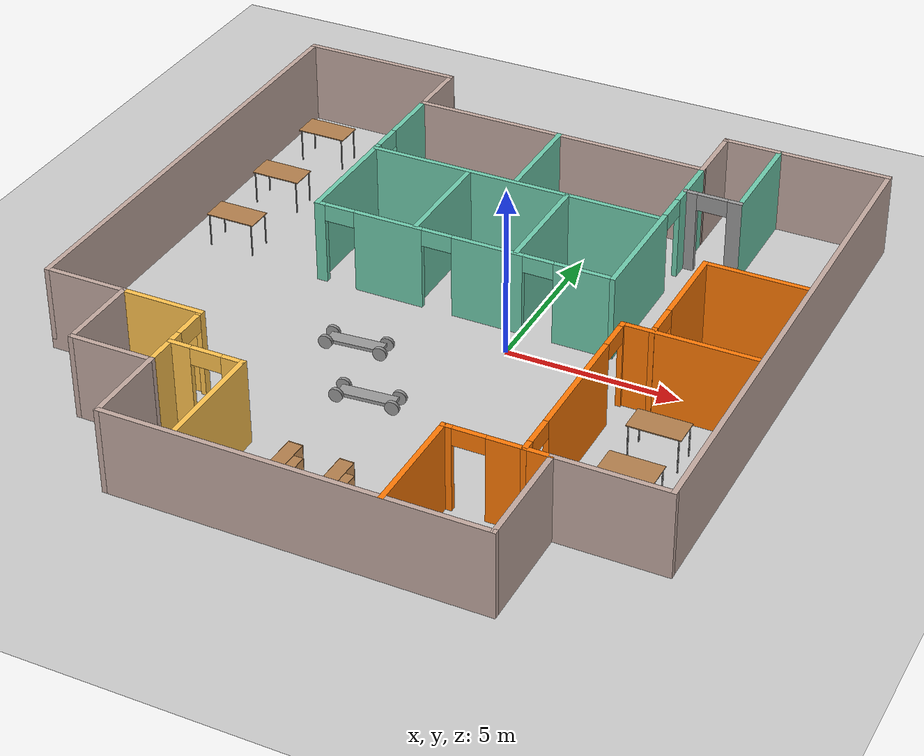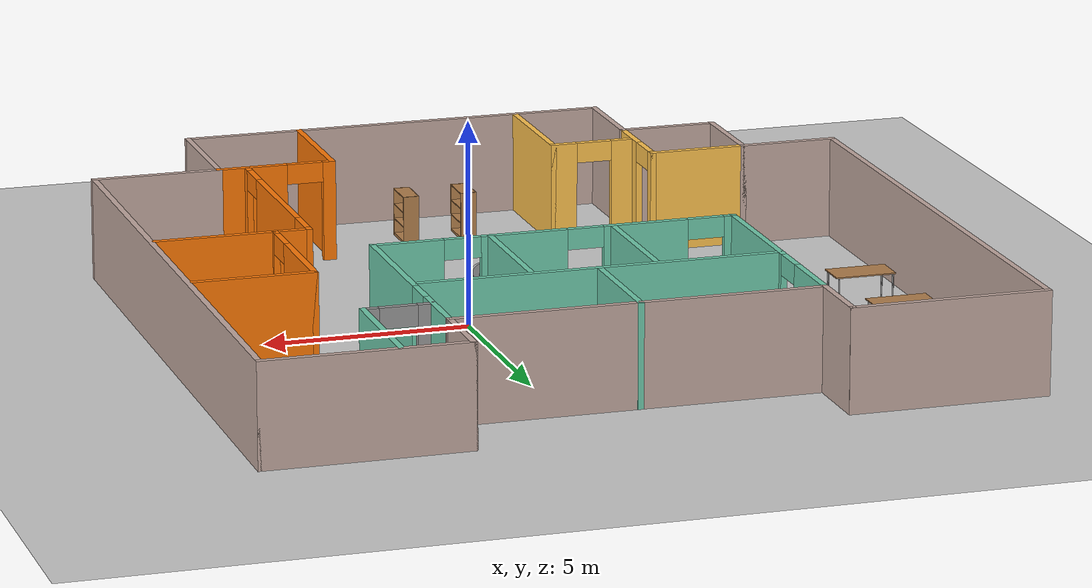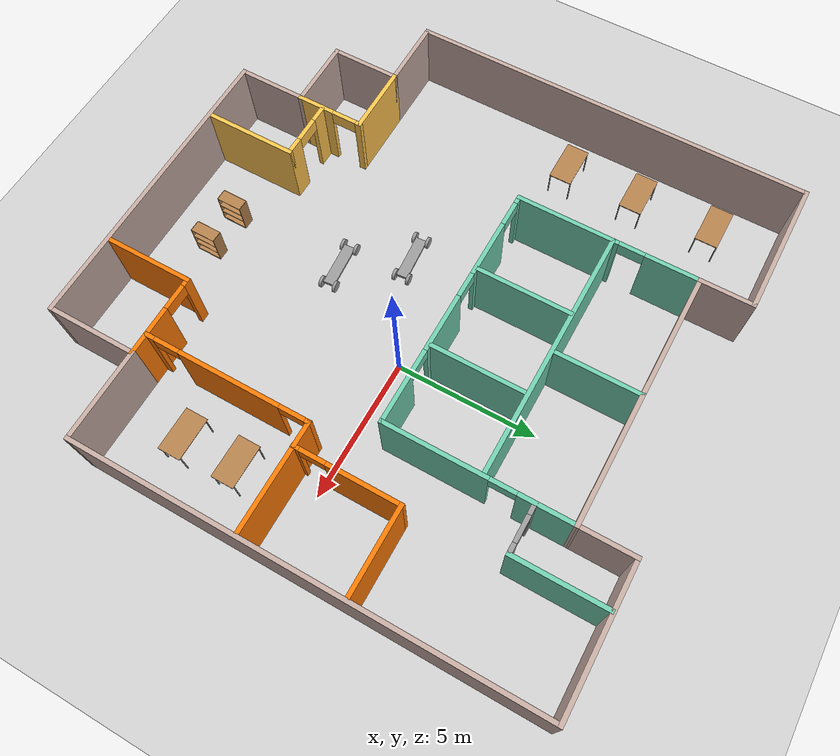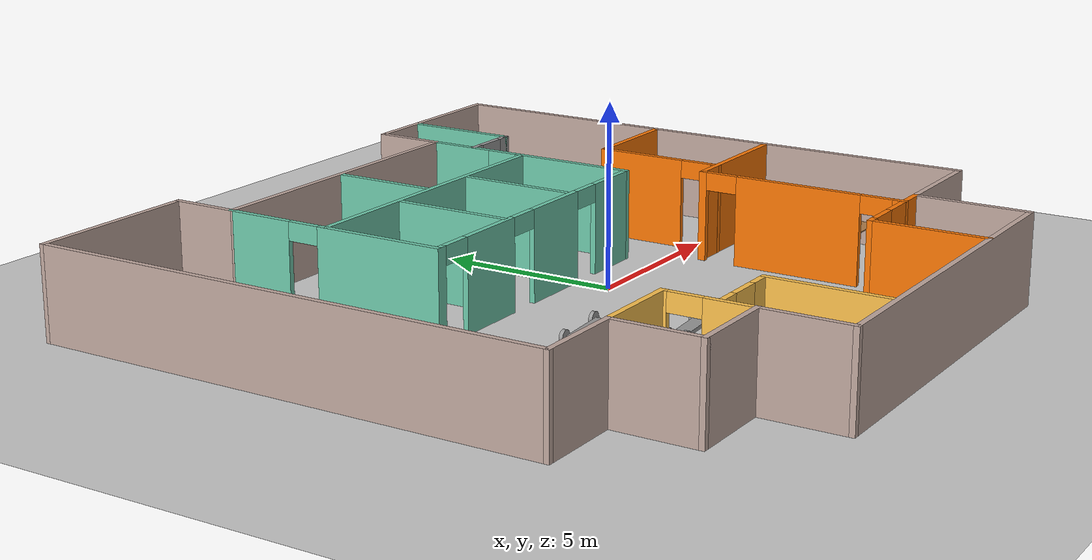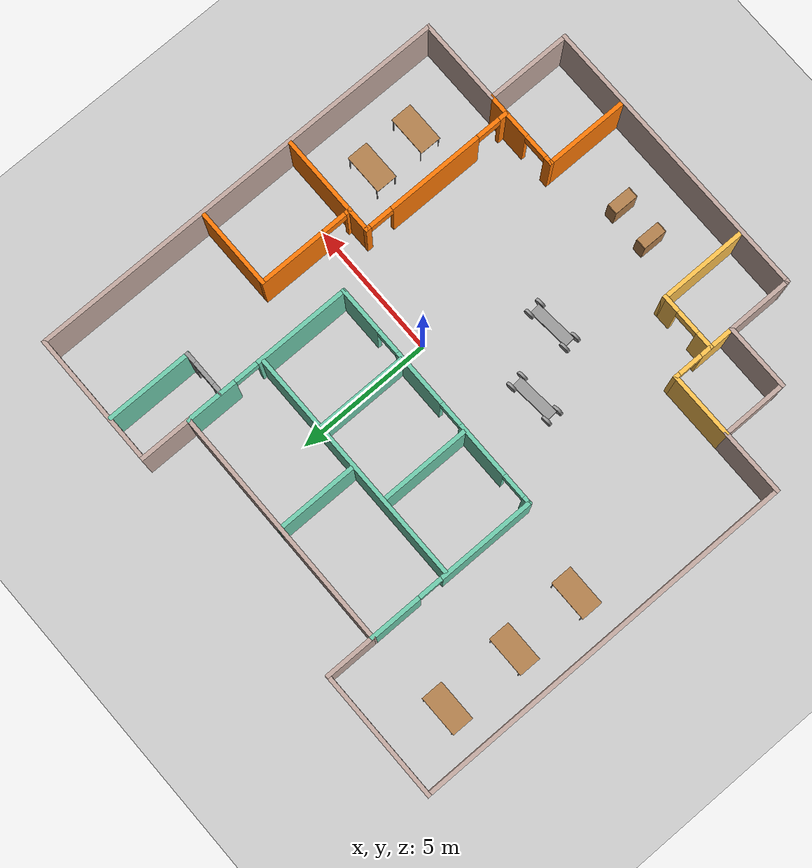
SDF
<sdf version="1.6">
 <world name="default">
  <plugin name="hello" filename="libhello.so"/>
  <light name="sun" type="directional">
   <pose>0 0 10 0 -0 0</pose>
   <diffuse>0.8 0.8 0.8 1</diffuse>
   <specular>0.2 0.2 0.2 1</specular>
   <attenuation>
    <range>1000</range>
    <constant>0.9</constant>
    <linear>0.01</linear>
    <quadratic>0.001</quadratic>
   </attenuation>
   <direction>-0.5 0.1 -0.9</direction>
  </light>
  <model name="ground_plane">
   <static>1</static>
   <link name="link">
    <collision name="collision">
     <geometry><plane><normal>0 0 1</normal><size>100 100</size></plane></geometry>
     <surface>
      <contact><collide_bitmask>65535</collide_bitmask></contact>
      <friction><ode><mu>100</mu><mu2>50</mu2></ode></friction>
     </surface>
    </collision>
    <visual name="visual">
     <cast_shadows>0</cast_shadows>
     <geometry><plane><normal>0 0 1</normal><size>100 100</size></plane></geometry>
     <material>
      <script><uri>file://media/materials/scripts/gazebo.material</uri><name>Gazebo/Grey</name></script>
     </material>
    </visual>
   </link>
  </model>
  <gravity>0 0 -9.8</gravity>
  <magnetic_field>6e-06 2.3e-05 -4.2e-05</magnetic_field>
  <atmosphere type="adiabatic"/>
  <physics name="default_physics" default="0" type="ode">
   <max_step_size>0.001</max_step_size>
   <real_time_factor>1</real_time_factor>
   <real_time_update_rate>1000</real_time_update_rate>
  </physics>
  <scene><ambient>0.4 0.4 0.4 1</ambient><background>0.7 0.7 0.7 1</background><shadows>1</shadows></scene>
  <spherical_coordinates>
   <surface_model>EARTH_WGS84</surface_model>
   <latitude_deg>0</latitude_deg>
   <longitude_deg>0</longitude_deg>
   <elevation>0</elevation>
   <heading_deg>0</heading_deg>
  </spherical_coordinates>
  <model name="mybuilding">
   <pose>-1.73634 -0.27598 0 0 -0 0</pose>
   <link name="Wall_0">
    <collision name="Wall_0_Collision">
     <geometry><box><size>4.85 0.15 2.5</size></box></geometry>
     <pose>0 0 1.25 0 -0 0</pose>
    </collision>
    <visual name="Wall_0_Visual">
     <pose>0 0 1.25 0 -0 0</pose>
     <geometry><box><size>4.85 0.15 2.5</size></box></geometry>
     <material>
      <script><uri>file://media/materials/scripts/gazebo.material</uri><name>Gazebo/Grey</name></script>
      <ambient>0.760784 0.662745 0.627451 1</ambient>
     </material>
     <meta><layer>0</layer></meta>
    </visual>
    <pose>-6.85 9.445 0 0 -0 0</pose>
   </link>
   <link name="Wall_1">
    <collision name="Wall_1_Collision">
     <geometry><box><size>1.92941 0.15 2.5</size></box></geometry>
     <pose>0 0 1.25 0 -0 0</pose>
    </collision>
    <visual name="Wall_1_Visual">
     <pose>0 0 1.25 0 -0 0</pose>
     <geometry><box><size>1.92941 0.15 2.5</size></box></geometry>
     <material>
      <script><uri>file://media/materials/scripts/gazebo.material</uri><name>Gazebo/Grey</name></script>
      <ambient>0.760784 0.662745 0.627451 1</ambient>
     </material>
     <meta><layer>0</layer></meta>
    </visual>
    <pose>-4.5 8.54529 0 0 0 -1.5708</pose>
   </link>
   <link name="Wall_10">
    <collision name="Wall_10_Collision">
     <geometry><box><size>10.75 0.15 2.5</size></box></geometry>
     <pose>0 0 1.25 0 -0 0</pose>
    </collision>
    <visual name="Wall_10_Visual">
     <pose>0 0 1.25 0 -0 0</pose>
     <geometry><box><size>10.75 0.15 2.5</size></box></geometry>
     <material>
      <script><uri>file://media/materials/scripts/gazebo.material</uri><name>Gazebo/Grey</name></script>
      <ambient>0.760784 0.662745 0.627451 1</ambient>
     </material>
     <meta><layer>0</layer></meta>
    </visual>
    <pose>0.8 -9.475 0 0 -0 3.14159</pose>
   </link>
   <link name="Wall_12">
    <collision name="Wall_12_Collision">
     <geometry><box><size>2.5 0.15 2.5</size></box></geometry>
     <pose>0 0 1.25 0 -0 0</pose>
    </collision>
    <visual name="Wall_12_Visual">
     <pose>0 0 1.25 0 -0 0</pose>
     <geometry><box><size>2.5 0.15 2.5</size></box></geometry>
     <material>
      <script><uri>file://media/materials/scripts/gazebo.material</uri><name>Gazebo/Grey</name></script>
      <ambient>0.760784 0.662745 0.627451 1</ambient>
     </material>
     <meta><layer>0</layer></meta>
    </visual>
    <pose>-4.5 -8.3 0 0 -0 1.5708</pose>
   </link>
   <link name="Wall_13">
    <collision name="Wall_13_Collision">
     <geometry><box><size>2.5 0.15 2.5</size></box></geometry>
     <pose>0 0 1.25 0 -0 0</pose>
    </collision>
    <visual name="Wall_13_Visual">
     <pose>0 0 1.25 0 -0 0</pose>
     <geometry><box><size>2.5 0.15 2.5</size></box></geometry>
     <material>
      <script><uri>file://media/materials/scripts/gazebo.material</uri><name>Gazebo/Grey</name></script>
      <ambient>0.760784 0.662745 0.627451 1</ambient>
     </material>
     <meta><layer>0</layer></meta>
    </visual>
    <pose>-5.675 -7.125 0 0 -0 3.14159</pose>
   </link>
   <link name="Wall_14">
    <collision name="Wall_14_Collision">
     <geometry><box><size>2.5 0.15 2.5</size></box></geometry>
     <pose>0 0 1.25 0 -0 0</pose>
    </collision>
    <visual name="Wall_14_Visual">
     <pose>0 0 1.25 0 -0 0</pose>
     <geometry><box><size>2.5 0.15 2.5</size></box></geometry>
     <material>
      <script><uri>file://media/materials/scripts/gazebo.material</uri><name>Gazebo/Grey</name></script>
      <ambient>0.760784 0.662745 0.627451 1</ambient>
     </material>
     <meta><layer>0</layer></meta>
    </visual>
    <pose>-6.85 -5.95 0 0 -0 1.5708</pose>
   </link>
   <link name="Wall_15">
    <collision name="Wall_15_Collision">
     <geometry><box><size>2.5 0.15 2.5</size></box></geometry>
     <pose>0 0 1.25 0 -0 0</pose>
    </collision>
    <visual name="Wall_15_Visual">
     <pose>0 0 1.25 0 -0 0</pose>
     <geometry><box><size>2.5 0.15 2.5</size></box></geometry>
     <material>
      <script><uri>file://media/materials/scripts/gazebo.material</uri><name>Gazebo/Grey</name></script>
      <ambient>0.760784 0.662745 0.627451 1</ambient>
     </material>
     <meta><layer>0</layer></meta>
    </visual>
    <pose>-8.025 -4.775 0 0 -0 3.14159</pose>
   </link>
   <link name="Wall_16">
    <collision name="Wall_16_Collision">
     <geometry><box><size>14.25 0.15 2.5</size></box></geometry>
     <pose>0 0 1.25 0 -0 0</pose>
    </collision>
    <visual name="Wall_16_Visual">
     <pose>0 0 1.25 0 -0 0</pose>
     <geometry><box><size>14.25 0.15 2.5</size></box></geometry>
     <material>
      <script><uri>file://media/materials/scripts/gazebo.material</uri><name>Gazebo/Grey</name></script>
      <ambient>0.760784 0.662745 0.627451 1</ambient>
     </material>
     <meta><layer>0</layer></meta>
    </visual>
    <pose>-9.2 2.275 0 0 -0 1.5708</pose>
   </link>
   <link name="Wall_18">
    <collision name="Wall_18_Collision">
     <geometry><box><size>2.5 0.15 2.5</size></box></geometry>
     <pose>0 0 1.25 0 -0 0</pose>
    </collision>
    <visual name="Wall_18_Visual">
     <pose>0 0 1.25 0 -0 0</pose>
     <geometry><box><size>2.5 0.15 2.5</size></box></geometry>
     <material>
      <script><uri>file://media/materials/scripts/gazebo.material</uri><name>Gazebo/Grey</name></script>
      <ambient>1 0.764706 0.305882 1</ambient>
     </material>
     <meta><layer>0</layer></meta>
    </visual>
    <pose>-5.675 -4.775 0 0 -0 0</pose>
   </link>
   <link name="Wall_19">
    <pose>-4.5 -5.95 0 0 0 -1.5708</pose>
    <visual name="Wall_19_Visual_0">
     <pose>-1.13558 0 1.25 0 -0 0</pose>
     <geometry><box><size>0.228848 0.15 2.5</size></box></geometry>
     <material>
      <script><uri>file://media/materials/scripts/gazebo.material</uri><name>Gazebo/Grey</name></script>
      <ambient>1 0.764706 0.305882 1</ambient>
     </material>
     <meta><layer>0</layer></meta>
    </visual>
    <collision name="Wall_19_Collision_0">
     <geometry><box><size>0.228848 0.15 2.5</size></box></geometry>
     <pose>-1.13558 0 1.25 0 -0 0</pose>
    </collision>
    <visual name="Wall_19_Visual_1">
     <pose>0.564424 0 1.25 0 -0 0</pose>
     <geometry><box><size>1.37115 0.15 2.5</size></box></geometry>
     <material>
      <script><uri>file://media/materials/scripts/gazebo.material</uri><name>Gazebo/Grey</name></script>
      <ambient>1 0.764706 0.305882 1</ambient>
     </material>
     <meta><layer>0</layer></meta>
    </visual>
    <collision name="Wall_19_Collision_1">
     <geometry><box><size>1.37115 0.15 2.5</size></box></geometry>
     <pose>0.564424 0 1.25 0 -0 0</pose>
    </collision>
    <visual name="Wall_19_Visual_2">
     <pose>-0.571152 0 2.25 0 -0 0</pose>
     <geometry><box><size>0.9 0.15 0.5</size></box></geometry>
     <material>
      <script><uri>file://media/materials/scripts/gazebo.material</uri><name>Gazebo/Grey</name></script>
      <ambient>1 0.764706 0.305882 1</ambient>
     </material>
     <meta><layer>0</layer></meta>
    </visual>
    <collision name="Wall_19_Collision_2">
     <geometry><box><size>0.9 0.15 0.5</size></box></geometry>
     <pose>-0.571152 0 2.25 0 -0 0</pose>
    </collision>
   </link>
   <link name="Wall_2">
    <collision name="Wall_2_Collision">
     <geometry><box><size>9 0.15 2.5</size></box></geometry>
     <pose>0 0 1.25 0 -0 0</pose>
    </collision>
    <visual name="Wall_2_Visual">
     <pose>0 0 1.25 0 -0 0</pose>
     <geometry><box><size>9 0.15 2.5</size></box></geometry>
     <material>
      <script><uri>file://media/materials/scripts/gazebo.material</uri><name>Gazebo/Grey</name></script>
      <ambient>0.760784 0.662745 0.627451 1</ambient>
     </material>
     <meta><layer>0</layer></meta>
    </visual>
    <pose>-0.075 7.6403 0 0 0 -0.003457</pose>
   </link>
   <link name="Wall_21">
    <pose>-3.43491 -6.23586 0 0 -0 0</pose>
    <visual name="Wall_21_Visual_0">
     <pose>-0.787798 0 1.25 0 -0 0</pose>
     <geometry><box><size>0.674404 0.15 2.5</size></box></geometry>
     <material>
      <script><uri>file://media/materials/scripts/gazebo.material</uri><name>Gazebo/Grey</name></script>
      <ambient>1 0.764706 0.305882 1</ambient>
     </material>
     <meta><layer>0</layer></meta>
    </visual>
    <collision name="Wall_21_Collision_0">
     <geometry><box><size>0.674404 0.15 2.5</size></box></geometry>
     <pose>-0.787798 0 1.25 0 -0 0</pose>
    </collision>
    <visual name="Wall_21_Visual_1">
     <pose>0.787202 0 1.25 0 -0 0</pose>
     <geometry><box><size>0.675596 0.15 2.5</size></box></geometry>
     <material>
      <script><uri>file://media/materials/scripts/gazebo.material</uri><name>Gazebo/Grey</name></script>
      <ambient>1 0.764706 0.305882 1</ambient>
     </material>
     <meta><layer>0</layer></meta>
    </visual>
    <collision name="Wall_21_Collision_1">
     <geometry><box><size>0.675596 0.15 2.5</size></box></geometry>
     <pose>0.787202 0 1.25 0 -0 0</pose>
    </collision>
    <visual name="Wall_21_Visual_2">
     <pose>-0.000596 0 2.25 0 -0 0</pose>
     <geometry><box><size>0.9 0.15 0.5</size></box></geometry>
     <material>
      <script><uri>file://media/materials/scripts/gazebo.material</uri><name>Gazebo/Grey</name></script>
      <ambient>1 0.764706 0.305882 1</ambient>
     </material>
     <meta><layer>0</layer></meta>
    </visual>
    <collision name="Wall_21_Collision_2">
     <geometry><box><size>0.9 0.15 0.5</size></box></geometry>
     <pose>-0.000596 0 2.25 0 -0 0</pose>
    </collision>
   </link>
   <link name="Wall_22">
    <collision name="Wall_22_Collision">
     <geometry><box><size>3.25 0.15 2.5</size></box></geometry>
     <pose>0 0 1.25 0 -0 0</pose>
    </collision>
    <visual name="Wall_22_Visual">
     <pose>0 0 1.25 0 -0 0</pose>
     <geometry><box><size>3.25 0.15 2.5</size></box></geometry>
     <material>
      <script><uri>file://media/materials/scripts/gazebo.material</uri><name>Gazebo/Grey</name></script>
      <ambient>1 0.764706 0.305882 1</ambient>
     </material>
     <meta><layer>0</layer></meta>
    </visual>
    <pose>-2.3849 -7.78586 0 0 0 -1.5708</pose>
   </link>
   <link name="Wall_24">
    <pose>4.675 -6.375 0 0 -0 3.14159</pose>
    <visual name="Wall_24_Visual_0">
     <pose>-0.610153 0 1.25 0 -0 0</pose>
     <geometry><box><size>1.77969 0.15 2.5</size></box></geometry>
     <material>
      <script><uri>file://media/materials/scripts/gazebo.material</uri><name>Gazebo/Grey</name></script>
      <ambient>0.996078 0.47451 0.0196078 1</ambient>
     </material>
     <meta><layer>0</layer></meta>
    </visual>
    <collision name="Wall_24_Collision_0">
     <geometry><box><size>1.77969 0.15 2.5</size></box></geometry>
     <pose>-0.610153 0 1.25 0 -0 0</pose>
    </collision>
    <visual name="Wall_24_Visual_1">
     <pose>1.33985 0 1.25 0 -0 0</pose>
     <geometry><box><size>0.320306 0.15 2.5</size></box></geometry>
     <material>
      <script><uri>file://media/materials/scripts/gazebo.material</uri><name>Gazebo/Grey</name></script>
      <ambient>0.996078 0.47451 0.0196078 1</ambient>
     </material>
     <meta><layer>0</layer></meta>
    </visual>
    <collision name="Wall_24_Collision_1">
     <geometry><box><size>0.320306 0.15 2.5</size></box></geometry>
     <pose>1.33985 0 1.25 0 -0 0</pose>
    </collision>
    <visual name="Wall_24_Visual_2">
     <pose>0.729694 0 2.25 0 -0 0</pose>
     <geometry><box><size>0.9 0.15 0.5</size></box></geometry>
     <material>
      <script><uri>file://media/materials/scripts/gazebo.material</uri><name>Gazebo/Grey</name></script>
      <ambient>0.996078 0.47451 0.0196078 1</ambient>
     </material>
     <meta><layer>0</layer></meta>
    </visual>
    <collision name="Wall_24_Collision_2">
     <geometry><box><size>0.9 0.15 0.5</size></box></geometry>
     <pose>0.729694 0 2.25 0 -0 0</pose>
    </collision>
   </link>
   <link name="Wall_25">
    <collision name="Wall_25_Collision">
     <geometry><box><size>3.25 0.15 2.5</size></box></geometry>
     <pose>0 0 1.25 0 -0 0</pose>
    </collision>
    <visual name="Wall_25_Visual">
     <pose>0 0 1.25 0 -0 0</pose>
     <geometry><box><size>3.25 0.15 2.5</size></box></geometry>
     <material>
      <script><uri>file://media/materials/scripts/gazebo.material</uri><name>Gazebo/Grey</name></script>
      <ambient>0.996078 0.47451 0.0196078 1</ambient>
     </material>
     <meta><layer>0</layer></meta>
    </visual>
    <pose>3.25 -7.925 0 0 0 -1.5708</pose>
   </link>
   <link name="Wall_28">
    <pose>5.39698 -3.45078 0 0 -0 1.5708</pose>
    <visual name="Wall_28_Visual_0">
     <pose>-2.81146 0 1.25 0 -0 0</pose>
     <geometry><box><size>0.377073 0.15 2.5</size></box></geometry>
     <material>
      <script><uri>file://media/materials/scripts/gazebo.material</uri><name>Gazebo/Grey</name></script>
      <ambient>0.996078 0.47451 0.0196078 1</ambient>
     </material>
     <meta><layer>0</layer></meta>
    </visual>
    <collision name="Wall_28_Collision_0">
     <geometry><box><size>0.377073 0.15 2.5</size></box></geometry>
     <pose>-2.81146 0 1.25 0 -0 0</pose>
    </collision>
    <visual name="Wall_28_Visual_1">
     <pose>0.080213 0 1.25 0 -0 0</pose>
     <geometry><box><size>3.60628 0.15 2.5</size></box></geometry>
     <material>
      <script><uri>file://media/materials/scripts/gazebo.material</uri><name>Gazebo/Grey</name></script>
      <ambient>0.996078 0.47451 0.0196078 1</ambient>
     </material>
     <meta><layer>0</layer></meta>
    </visual>
    <collision name="Wall_28_Collision_1">
     <geometry><box><size>3.60628 0.15 2.5</size></box></geometry>
     <pose>0.080213 0 1.25 0 -0 0</pose>
    </collision>
    <visual name="Wall_28_Visual_2">
     <pose>2.89168 0 1.25 0 -0 0</pose>
     <geometry><box><size>0.216648 0.15 2.5</size></box></geometry>
     <material>
      <script><uri>file://media/materials/scripts/gazebo.material</uri><name>Gazebo/Grey</name></script>
      <ambient>0.996078 0.47451 0.0196078 1</ambient>
     </material>
     <meta><layer>0</layer></meta>
    </visual>
    <collision name="Wall_28_Collision_2">
     <geometry><box><size>0.216648 0.15 2.5</size></box></geometry>
     <pose>2.89168 0 1.25 0 -0 0</pose>
    </collision>
    <visual name="Wall_28_Visual_3">
     <pose>-2.17293 0 2.25 0 -0 0</pose>
     <geometry><box><size>0.9 0.15 0.5</size></box></geometry>
     <material>
      <script><uri>file://media/materials/scripts/gazebo.material</uri><name>Gazebo/Grey</name></script>
      <ambient>0.996078 0.47451 0.0196078 1</ambient>
     </material>
     <meta><layer>0</layer></meta>
    </visual>
    <collision name="Wall_28_Collision_3">
     <geometry><box><size>0.9 0.15 0.5</size></box></geometry>
     <pose>-2.17293 0 2.25 0 -0 0</pose>
    </collision>
    <visual name="Wall_28_Visual_4">
     <pose>2.33335 0 2.25 0 -0 0</pose>
     <geometry><box><size>0.9 0.15 0.5</size></box></geometry>
     <material>
      <script><uri>file://media/materials/scripts/gazebo.material</uri><name>Gazebo/Grey</name></script>
      <ambient>0.996078 0.47451 0.0196078 1</ambient>
     </material>
     <meta><layer>0</layer></meta>
    </visual>
    <collision name="Wall_28_Collision_4">
     <geometry><box><size>0.9 0.15 0.5</size></box></geometry>
     <pose>2.33335 0 2.25 0 -0 0</pose>
    </collision>
   </link>
   <link name="Wall_3">
    <collision name="Wall_3_Collision">
     <geometry><box><size>2 0.15 2.5</size></box></geometry>
     <pose>0 0 1.25 0 -0 0</pose>
    </collision>
    <visual name="Wall_3_Visual">
     <pose>0 0 1.25 0 -0 0</pose>
     <geometry><box><size>2 0.15 2.5</size></box></geometry>
     <material>
      <script><uri>file://media/materials/scripts/gazebo.material</uri><name>Gazebo/Grey</name></script>
      <ambient>0.760784 0.662745 0.627451 1</ambient>
     </material>
     <meta><layer>0</layer></meta>
    </visual>
    <pose>4.35 8.55 0 0 -0 1.5708</pose>
   </link>
   <link name="Wall_32">
    <collision name="Wall_32_Collision">
     <geometry><box><size>3.85 0.15 2.5</size></box></geometry>
     <pose>0 0 1.25 0 -0 0</pose>
    </collision>
    <visual name="Wall_32_Visual">
     <pose>0 0 1.25 0 -0 0</pose>
     <geometry><box><size>3.85 0.15 2.5</size></box></geometry>
     <material>
      <script><uri>file://media/materials/scripts/gazebo.material</uri><name>Gazebo/Grey</name></script>
      <ambient>0.996078 0.47451 0.0196078 1</ambient>
     </material>
     <meta><layer>0</layer></meta>
    </visual>
    <pose>7.24698 -0.525782 0 0 -0 0</pose>
   </link>
   <link name="Wall_34">
    <pose>-4.5 4.48059 0 0 0 -1.5708</pose>
    <visual name="Wall_34_Visual_0">
     <pose>-2.27107 0 1.25 0 -0 0</pose>
     <geometry><box><size>1.95787 0.15 2.5</size></box></geometry>
     <material>
      <script><uri>file://media/materials/scripts/gazebo.material</uri><name>Gazebo/Grey</name></script>
      <ambient>0.435294 0.796078 0.67451 1</ambient>
     </material>
     <meta><layer>0</layer></meta>
    </visual>
    <collision name="Wall_34_Collision_0">
     <geometry><box><size>1.95787 0.15 2.5</size></box></geometry>
     <pose>-2.27107 0 1.25 0 -0 0</pose>
    </collision>
    <visual name="Wall_34_Visual_1">
     <pose>1.42893 0 1.25 0 -0 0</pose>
     <geometry><box><size>3.64213 0.15 2.5</size></box></geometry>
     <material>
      <script><uri>file://media/materials/scripts/gazebo.material</uri><name>Gazebo/Grey</name></script>
      <ambient>0.435294 0.796078 0.67451 1</ambient>
     </material>
     <meta><layer>0</layer></meta>
    </visual>
    <collision name="Wall_34_Collision_1">
     <geometry><box><size>3.64213 0.15 2.5</size></box></geometry>
     <pose>1.42893 0 1.25 0 -0 0</pose>
    </collision>
    <visual name="Wall_34_Visual_2">
     <pose>-0.842134 0 2.25 0 -0 0</pose>
     <geometry><box><size>0.9 0.15 0.5</size></box></geometry>
     <material>
      <script><uri>file://media/materials/scripts/gazebo.material</uri><name>Gazebo/Grey</name></script>
      <ambient>0.435294 0.796078 0.67451 1</ambient>
     </material>
     <meta><layer>0</layer></meta>
    </visual>
    <collision name="Wall_34_Collision_2">
     <geometry><box><size>0.9 0.15 0.5</size></box></geometry>
     <pose>-0.842134 0 2.25 0 -0 0</pose>
    </collision>
   </link>
   <link name="Wall_36">
    <pose>-0.075 1.30559 0 0 -0 0</pose>
    <visual name="Wall_36_Visual_0">
     <pose>-4.3354 0 1.25 0 -0 0</pose>
     <geometry><box><size>0.329192 0.15 2.5</size></box></geometry>
     <material>
      <script><uri>file://media/materials/scripts/gazebo.material</uri><name>Gazebo/Grey</name></script>
      <ambient>0.435294 0.796078 0.67451 1</ambient>
     </material>
     <meta><layer>0</layer></meta>
    </visual>
    <collision name="Wall_36_Collision_0">
     <geometry><box><size>0.329192 0.15 2.5</size></box></geometry>
     <pose>-4.3354 0 1.25 0 -0 0</pose>
    </collision>
    <visual name="Wall_36_Visual_1">
     <pose>-2.23035 0 1.25 0 -0 0</pose>
     <geometry><box><size>2.08092 0.15 2.5</size></box></geometry>
     <material>
      <script><uri>file://media/materials/scripts/gazebo.material</uri><name>Gazebo/Grey</name></script>
      <ambient>0.435294 0.796078 0.67451 1</ambient>
     </material>
     <meta><layer>0</layer></meta>
    </visual>
    <collision name="Wall_36_Collision_1">
     <geometry><box><size>2.08092 0.15 2.5</size></box></geometry>
     <pose>-2.23035 0 1.25 0 -0 0</pose>
    </collision>
    <visual name="Wall_36_Visual_2">
     <pose>0.765773 0 1.25 0 -0 0</pose>
     <geometry><box><size>2.11133 0.15 2.5</size></box></geometry>
     <material>
      <script><uri>file://media/materials/scripts/gazebo.material</uri><name>Gazebo/Grey</name></script>
      <ambient>0.435294 0.796078 0.67451 1</ambient>
     </material>
     <meta><layer>0</layer></meta>
    </visual>
    <collision name="Wall_36_Collision_2">
     <geometry><box><size>2.11133 0.15 2.5</size></box></geometry>
     <pose>0.765773 0 1.25 0 -0 0</pose>
    </collision>
    <visual name="Wall_36_Visual_3">
     <pose>3.61072 0 1.25 0 -0 0</pose>
     <geometry><box><size>1.77856 0.15 2.5</size></box></geometry>
     <material>
      <script><uri>file://media/materials/scripts/gazebo.material</uri><name>Gazebo/Grey</name></script>
      <ambient>0.435294 0.796078 0.67451 1</ambient>
     </material>
     <meta><layer>0</layer></meta>
    </visual>
    <collision name="Wall_36_Collision_3">
     <geometry><box><size>1.77856 0.15 2.5</size></box></geometry>
     <pose>3.61072 0 1.25 0 -0 0</pose>
    </collision>
    <visual name="Wall_36_Visual_4">
     <pose>-3.72081 0 2.25 0 -0 0</pose>
     <geometry><box><size>0.9 0.15 0.5</size></box></geometry>
     <material>
      <script><uri>file://media/materials/scripts/gazebo.material</uri><name>Gazebo/Grey</name></script>
      <ambient>0.435294 0.796078 0.67451 1</ambient>
     </material>
     <meta><layer>0</layer></meta>
    </visual>
    <collision name="Wall_36_Collision_4">
     <geometry><box><size>0.9 0.15 0.5</size></box></geometry>
     <pose>-3.72081 0 2.25 0 -0 0</pose>
    </collision>
    <visual name="Wall_36_Visual_5">
     <pose>-0.739893 0 2.25 0 -0 0</pose>
     <geometry><box><size>0.9 0.15 0.5</size></box></geometry>
     <material>
      <script><uri>file://media/materials/scripts/gazebo.material</uri><name>Gazebo/Grey</name></script>
      <ambient>0.435294 0.796078 0.67451 1</ambient>
     </material>
     <meta><layer>0</layer></meta>
    </visual>
    <collision name="Wall_36_Collision_5">
     <geometry><box><size>0.9 0.15 0.5</size></box></geometry>
     <pose>-0.739893 0 2.25 0 -0 0</pose>
    </collision>
    <visual name="Wall_36_Visual_6">
     <pose>2.27144 0 2.25 0 -0 0</pose>
     <geometry><box><size>0.9 0.15 0.5</size></box></geometry>
     <material>
      <script><uri>file://media/materials/scripts/gazebo.material</uri><name>Gazebo/Grey</name></script>
      <ambient>0.435294 0.796078 0.67451 1</ambient>
     </material>
     <meta><layer>0</layer></meta>
    </visual>
    <collision name="Wall_36_Collision_6">
     <geometry><box><size>0.9 0.15 0.5</size></box></geometry>
     <pose>2.27144 0 2.25 0 -0 0</pose>
    </collision>
   </link>
   <link name="Wall_39">
    <pose>4.35 4.46529 0 0 -0 1.5708</pose>
    <visual name="Wall_39_Visual_0">
     <pose>-1.42238 0 1.25 0 -0 0</pose>
     <geometry><box><size>3.62464 0.15 2.5</size></box></geometry>
     <material>
      <script><uri>file://media/materials/scripts/gazebo.material</uri><name>Gazebo/Grey</name></script>
      <ambient>0.435294 0.796078 0.67451 1</ambient>
     </material>
     <meta><layer>0</layer></meta>
    </visual>
    <collision name="Wall_39_Collision_0">
     <geometry><box><size>3.62464 0.15 2.5</size></box></geometry>
     <pose>-1.42238 0 1.25 0 -0 0</pose>
    </collision>
    <visual name="Wall_39_Visual_1">
     <pose>2.26232 0 1.25 0 -0 0</pose>
     <geometry><box><size>1.94477 0.15 2.5</size></box></geometry>
     <material>
      <script><uri>file://media/materials/scripts/gazebo.material</uri><name>Gazebo/Grey</name></script>
      <ambient>0.435294 0.796078 0.67451 1</ambient>
     </material>
     <meta><layer>0</layer></meta>
    </visual>
    <collision name="Wall_39_Collision_1">
     <geometry><box><size>1.94477 0.15 2.5</size></box></geometry>
     <pose>2.26232 0 1.25 0 -0 0</pose>
    </collision>
    <visual name="Wall_39_Visual_2">
     <pose>0.839939 0 2.25 0 -0 0</pose>
     <geometry><box><size>0.9 0.15 0.5</size></box></geometry>
     <material>
      <script><uri>file://media/materials/scripts/gazebo.material</uri><name>Gazebo/Grey</name></script>
      <ambient>0.435294 0.796078 0.67451 1</ambient>
     </material>
     <meta><layer>0</layer></meta>
    </visual>
    <collision name="Wall_39_Collision_2">
     <geometry><box><size>0.9 0.15 0.5</size></box></geometry>
     <pose>0.839939 0 2.25 0 -0 0</pose>
    </collision>
   </link>
   <link name="Wall_4">
    <collision name="Wall_4_Collision">
     <geometry><box><size>5 0.15 2.5</size></box></geometry>
     <pose>0 0 1.25 0 -0 0</pose>
    </collision>
    <visual name="Wall_4_Visual">
     <pose>0 0 1.25 0 -0 0</pose>
     <geometry><box><size>5 0.15 2.5</size></box></geometry>
     <material>
      <script><uri>file://media/materials/scripts/gazebo.material</uri><name>Gazebo/Grey</name></script>
      <ambient>0.760784 0.662745 0.627451 1</ambient>
     </material>
     <meta><layer>0</layer></meta>
    </visual>
    <pose>6.775 9.475 0 0 -0 0</pose>
   </link>
   <link name="Wall_41">
    <collision name="Wall_41_Collision">
     <geometry><box><size>8.85 0.15 2.5</size></box></geometry>
     <pose>0 0 1.25 0 -0 0</pose>
    </collision>
    <visual name="Wall_41_Visual">
     <pose>0 0 1.25 0 -0 0</pose>
     <geometry><box><size>8.85 0.15 2.5</size></box></geometry>
     <material>
      <script><uri>file://media/materials/scripts/gazebo.material</uri><name>Gazebo/Grey</name></script>
      <ambient>0.435294 0.796078 0.67451 1</ambient>
     </material>
     <meta><layer>0</layer></meta>
    </visual>
    <pose>-0.116418 4.65945 0 0 -0 0</pose>
   </link>
   <link name="Wall_43">
    <collision name="Wall_43_Collision">
     <geometry><box><size>3 0.15 2.5</size></box></geometry>
     <pose>0 0 1.25 0 -0 0</pose>
    </collision>
    <visual name="Wall_43_Visual">
     <pose>0 0 1.25 0 -0 0</pose>
     <geometry><box><size>3 0.15 2.5</size></box></geometry>
     <material>
      <script><uri>file://media/materials/scripts/gazebo.material</uri><name>Gazebo/Grey</name></script>
      <ambient>0.435294 0.796078 0.67451 1</ambient>
     </material>
     <meta><layer>0</layer></meta>
    </visual>
    <pose>-0.095849 6.22004 0 0 0 -1.5708</pose>
   </link>
   <link name="Wall_45">
    <collision name="Wall_45_Collision">
     <geometry><box><size>3.35 0.15 2.5</size></box></geometry>
     <pose>0 0 1.25 0 -0 0</pose>
    </collision>
    <visual name="Wall_45_Visual">
     <pose>0 0 1.25 0 -0 0</pose>
     <geometry><box><size>3.35 0.15 2.5</size></box></geometry>
     <material>
      <script><uri>file://media/materials/scripts/gazebo.material</uri><name>Gazebo/Grey</name></script>
      <ambient>0.435294 0.796078 0.67451 1</ambient>
     </material>
     <meta><layer>0</layer></meta>
    </visual>
    <pose>-1.49929 3.00734 0 0 0 -1.5708</pose>
   </link>
   <link name="Wall_5">
    <collision name="Wall_5_Collision">
     <geometry><box><size>16 0.15 2.5</size></box></geometry>
     <pose>0 0 1.25 0 -0 0</pose>
    </collision>
    <visual name="Wall_5_Visual">
     <pose>0 0 1.25 0 -0 0</pose>
     <geometry><box><size>16 0.15 2.5</size></box></geometry>
     <material>
      <script><uri>file://media/materials/scripts/gazebo.material</uri><name>Gazebo/Grey</name></script>
      <ambient>0.760784 0.662745 0.627451 1</ambient>
     </material>
     <meta><layer>0</layer></meta>
    </visual>
    <pose>9.2 1.55 0 0 0 -1.5708</pose>
   </link>
   <link name="Wall_50">
    <collision name="Wall_50_Collision">
     <geometry><box><size>3.35 0.15 2.5</size></box></geometry>
     <pose>0 0 1.25 0 -0 0</pose>
    </collision>
    <visual name="Wall_50_Visual">
     <pose>0 0 1.25 0 -0 0</pose>
     <geometry><box><size>3.35 0.15 2.5</size></box></geometry>
     <material>
      <script><uri>file://media/materials/scripts/gazebo.material</uri><name>Gazebo/Grey</name></script>
      <ambient>0.435294 0.796078 0.67451 1</ambient>
     </material>
     <meta><layer>0</layer></meta>
    </visual>
    <pose>1.51205 2.99214 0 0 0 -1.5708</pose>
   </link>
   <link name="Wall_53">
    <pose>5.18156 6.317 0 0 -0 0</pose>
    <visual name="Wall_53_Visual_0">
     <pose>-0.664994 0 1.25 0 -0 0</pose>
     <geometry><box><size>0.420012 0.15 2.5</size></box></geometry>
     <material>
      <script><uri>file://media/materials/scripts/gazebo.material</uri><name>Gazebo/Grey</name></script>
      <ambient>1 1 1 1</ambient>
     </material>
     <meta><layer>0</layer></meta>
    </visual>
    <collision name="Wall_53_Collision_0">
     <geometry><box><size>0.420012 0.15 2.5</size></box></geometry>
     <pose>-0.664994 0 1.25 0 -0 0</pose>
    </collision>
    <visual name="Wall_53_Visual_1">
     <pose>0.660006 0 1.25 0 -0 0</pose>
     <geometry><box><size>0.429988 0.15 2.5</size></box></geometry>
     <material>
      <script><uri>file://media/materials/scripts/gazebo.material</uri><name>Gazebo/Grey</name></script>
      <ambient>1 1 1 1</ambient>
     </material>
     <meta><layer>0</layer></meta>
    </visual>
    <collision name="Wall_53_Collision_1">
     <geometry><box><size>0.429988 0.15 2.5</size></box></geometry>
     <pose>0.660006 0 1.25 0 -0 0</pose>
    </collision>
    <visual name="Wall_53_Visual_2">
     <pose>-0.004988 0 2.25 0 -0 0</pose>
     <geometry><box><size>0.9 0.15 0.5</size></box></geometry>
     <material>
      <script><uri>file://media/materials/scripts/gazebo.material</uri><name>Gazebo/Grey</name></script>
      <ambient>1 1 1 1</ambient>
     </material>
     <meta><layer>0</layer></meta>
    </visual>
    <collision name="Wall_53_Collision_2">
     <geometry><box><size>0.9 0.15 0.5</size></box></geometry>
     <pose>-0.004988 0 2.25 0 -0 0</pose>
    </collision>
   </link>
   <link name="Wall_54">
    <collision name="Wall_54_Collision">
     <geometry><box><size>3.25 0.15 2.5</size></box></geometry>
     <pose>0 0 1.25 0 -0 0</pose>
    </collision>
    <visual name="Wall_54_Visual">
     <pose>0 0 1.25 0 -0 0</pose>
     <geometry><box><size>3.25 0.15 2.5</size></box></geometry>
     <material>
      <script><uri>file://media/materials/scripts/gazebo.material</uri><name>Gazebo/Grey</name></script>
      <ambient>0.435294 0.796078 0.67451 1</ambient>
     </material>
     <meta><layer>0</layer></meta>
    </visual>
    <pose>5.98156 7.867 0 0 -0 1.5708</pose>
   </link>
   <link name="Wall_58">
    <pose>6.22247 1.26586 0 0 -0 1.5708</pose>
    <visual name="Wall_58_Visual_0">
     <pose>-1.74068 0 1.25 0 -0 0</pose>
     <geometry><box><size>0.268634 0.15 2.5</size></box></geometry>
     <material>
      <script><uri>file://media/materials/scripts/gazebo.material</uri><name>Gazebo/Grey</name></script>
      <ambient>0.996078 0.47451 0.0196078 1</ambient>
     </material>
     <meta><layer>0</layer></meta>
    </visual>
    <collision name="Wall_58_Collision_0">
     <geometry><box><size>0.268634 0.15 2.5</size></box></geometry>
     <pose>-1.74068 0 1.25 0 -0 0</pose>
    </collision>
    <visual name="Wall_58_Visual_1">
     <pose>0.584317 0 1.25 0 -0 0</pose>
     <geometry><box><size>2.58137 0.15 2.5</size></box></geometry>
     <material>
      <script><uri>file://media/materials/scripts/gazebo.material</uri><name>Gazebo/Grey</name></script>
      <ambient>0.996078 0.47451 0.0196078 1</ambient>
     </material>
     <meta><layer>0</layer></meta>
    </visual>
    <collision name="Wall_58_Collision_1">
     <geometry><box><size>2.58137 0.15 2.5</size></box></geometry>
     <pose>0.584317 0 1.25 0 -0 0</pose>
    </collision>
    <visual name="Wall_58_Visual_2">
     <pose>-1.15637 0 2.25 0 -0 0</pose>
     <geometry><box><size>0.9 0.15 0.5</size></box></geometry>
     <material>
      <script><uri>file://media/materials/scripts/gazebo.material</uri><name>Gazebo/Grey</name></script>
      <ambient>0.996078 0.47451 0.0196078 1</ambient>
     </material>
     <meta><layer>0</layer></meta>
    </visual>
    <collision name="Wall_58_Collision_2">
     <geometry><box><size>0.9 0.15 0.5</size></box></geometry>
     <pose>-1.15637 0 2.25 0 -0 0</pose>
    </collision>
   </link>
   <link name="Wall_59">
    <collision name="Wall_59_Collision">
     <geometry><box><size>3 0.15 2.5</size></box></geometry>
     <pose>0 0 1.25 0 -0 0</pose>
    </collision>
    <visual name="Wall_59_Visual">
     <pose>0 0 1.25 0 -0 0</pose>
     <geometry><box><size>3 0.15 2.5</size></box></geometry>
     <material>
      <script><uri>file://media/materials/scripts/gazebo.material</uri><name>Gazebo/Grey</name></script>
      <ambient>0.996078 0.47451 0.0196078 1</ambient>
     </material>
     <meta><layer>0</layer></meta>
    </visual>
    <pose>7.64747 3.06586 0 0 -0 0</pose>
   </link>
   <link name="Wall_7">
    <collision name="Wall_7_Collision">
     <geometry><box><size>3.25 0.15 2.5</size></box></geometry>
     <pose>0 0 1.25 0 -0 0</pose>
    </collision>
    <visual name="Wall_7_Visual">
     <pose>0 0 1.25 0 -0 0</pose>
     <geometry><box><size>3.25 0.15 2.5</size></box></geometry>
     <material>
      <script><uri>file://media/materials/scripts/gazebo.material</uri><name>Gazebo/Grey</name></script>
      <ambient>0.760784 0.662745 0.627451 1</ambient>
     </material>
     <meta><layer>0</layer></meta>
    </visual>
    <pose>7.65 -6.375 0 0 -0 3.14159</pose>
   </link>
   <link name="Wall_9">
    <collision name="Wall_9_Collision">
     <geometry><box><size>3.25 0.15 2.5</size></box></geometry>
     <pose>0 0 1.25 0 -0 0</pose>
    </collision>
    <visual name="Wall_9_Visual">
     <pose>0 0 1.25 0 -0 0</pose>
     <geometry><box><size>3.25 0.15 2.5</size></box></geometry>
     <material>
      <script><uri>file://media/materials/scripts/gazebo.material</uri><name>Gazebo/Grey</name></script>
      <ambient>0.760784 0.662745 0.627451 1</ambient>
     </material>
     <meta><layer>0</layer></meta>
    </visual>
    <pose>6.1 -7.925 0 0 0 -1.5708</pose>
   </link>
   <static>1</static>
  </model>
  <model name="table">
   <static>1</static>
   <link name="link">
    <collision name="surface">
     <pose>0 0 1 0 -0 0</pose>
     <geometry><box><size>1.5 0.8 0.03</size></box></geometry>
     <surface><friction><ode><mu>0.6</mu><mu2>0.6</mu2></ode></friction></surface>
    </collision>
    <visual name="visual1">
     <pose>0 0 1 0 -0 0</pose>
     <geometry><box><size>1.5 0.8 0.03</size></box></geometry>
     <material>
      <script><uri>file://media/materials/scripts/gazebo.material</uri><name>Gazebo/Wood</name></script>
     </material>
    </visual>
    <collision name="front_left_leg">
     <pose>0.68 0.38 0.5 0 -0 0</pose>
     <geometry><cylinder><radius>0.02</radius><length>1</length></cylinder></geometry>
    </collision>
    <visual name="front_left_leg">
     <pose>0.68 0.38 0.5 0 -0 0</pose>
     <geometry><cylinder><radius>0.02</radius><length>1</length></cylinder></geometry>
     <material>
      <script><uri>file://media/materials/scripts/gazebo.material</uri><name>Gazebo/Grey</name></script>
     </material>
    </visual>
    <collision name="front_right_leg">
     <pose>0.68 -0.38 0.5 0 -0 0</pose>
     <geometry><cylinder><radius>0.02</radius><length>1</length></cylinder></geometry>
    </collision>
    <visual name="front_right_leg">
     <pose>0.68 -0.38 0.5 0 -0 0</pose>
     <geometry><cylinder><radius>0.02</radius><length>1</length></cylinder></geometry>
     <material>
      <script><uri>file://media/materials/scripts/gazebo.material</uri><name>Gazebo/Grey</name></script>
     </material>
    </visual>
    <collision name="back_right_leg">
     <pose>-0.68 -0.38 0.5 0 -0 0</pose>
     <geometry><cylinder><radius>0.02</radius><length>1</length></cylinder></geometry>
    </collision>
    <visual name="back_right_leg">
     <pose>-0.68 -0.38 0.5 0 -0 0</pose>
     <geometry><cylinder><radius>0.02</radius><length>1</length></cylinder></geometry>
     <material>
      <script><uri>file://media/materials/scripts/gazebo.material</uri><name>Gazebo/Grey</name></script>
     </material>
    </visual>
    <collision name="back_left_leg">
     <pose>-0.68 0.38 0.5 0 -0 0</pose>
     <geometry><cylinder><radius>0.02</radius><length>1</length></cylinder></geometry>
    </collision>
    <visual name="back_left_leg">
     <pose>-0.68 0.38 0.5 0 -0 0</pose>
     <geometry><cylinder><radius>0.02</radius><length>1</length></cylinder></geometry>
     <material>
      <script><uri>file://media/materials/scripts/gazebo.material</uri><name>Gazebo/Grey</name></script>
     </material>
    </visual>
   </link>
   <pose>5.48664 -4.41852 0 0 -0 0</pose>
  </model>
  <model name="table_clone_0">
   <static>1</static>
   <link name="link">
    <collision name="surface">
     <pose>0 0 1 0 -0 0</pose>
     <geometry><box><size>1.5 0.8 0.03</size></box></geometry>
     <surface><friction><ode><mu>0.6</mu><mu2>0.6</mu2></ode></friction></surface>
    </collision>
    <visual name="visual1">
     <pose>0 0 1 0 -0 0</pose>
     <geometry><box><size>1.5 0.8 0.03</size></box></geometry>
     <material>
      <script><uri>file://media/materials/scripts/gazebo.material</uri><name>Gazebo/Wood</name></script>
     </material>
    </visual>
    <collision name="front_left_leg">
     <pose>0.68 0.38 0.5 0 -0 0</pose>
     <geometry><cylinder><radius>0.02</radius><length>1</length></cylinder></geometry>
    </collision>
    <visual name="front_left_leg">
     <pose>0.68 0.38 0.5 0 -0 0</pose>
     <geometry><cylinder><radius>0.02</radius><length>1</length></cylinder></geometry>
     <material>
      <script><uri>file://media/materials/scripts/gazebo.material</uri><name>Gazebo/Grey</name></script>
     </material>
    </visual>
    <collision name="front_right_leg">
     <pose>0.68 -0.38 0.5 0 -0 0</pose>
     <geometry><cylinder><radius>0.02</radius><length>1</length></cylinder></geometry>
    </collision>
    <visual name="front_right_leg">
     <pose>0.68 -0.38 0.5 0 -0 0</pose>
     <geometry><cylinder><radius>0.02</radius><length>1</length></cylinder></geometry>
     <material>
      <script><uri>file://media/materials/scripts/gazebo.material</uri><name>Gazebo/Grey</name></script>
     </material>
    </visual>
    <collision name="back_right_leg">
     <pose>-0.68 -0.38 0.5 0 -0 0</pose>
     <geometry><cylinder><radius>0.02</radius><length>1</length></cylinder></geometry>
    </collision>
    <visual name="back_right_leg">
     <pose>-0.68 -0.38 0.5 0 -0 0</pose>
     <geometry><cylinder><radius>0.02</radius><length>1</length></cylinder></geometry>
     <material>
      <script><uri>file://media/materials/scripts/gazebo.material</uri><name>Gazebo/Grey</name></script>
     </material>
    </visual>
    <collision name="back_left_leg">
     <pose>-0.68 0.38 0.5 0 -0 0</pose>
     <geometry><cylinder><radius>0.02</radius><length>1</length></cylinder></geometry>
    </collision>
    <visual name="back_left_leg">
     <pose>-0.68 0.38 0.5 0 -0 0</pose>
     <geometry><cylinder><radius>0.02</radius><length>1</length></cylinder></geometry>
     <material>
      <script><uri>file://media/materials/scripts/gazebo.material</uri><name>Gazebo/Grey</name></script>
     </material>
    </visual>
   </link>
   <pose>5.43526 -2.5035 0 0 -0 0</pose>
  </model>
  <model name="table_0">
   <static>1</static>
   <link name="link">
    <collision name="surface">
     <pose>0 0 1 0 -0 0</pose>
     <geometry><box><size>1.5 0.8 0.03</size></box></geometry>
     <surface><friction><ode><mu>0.6</mu><mu2>0.6</mu2></ode></friction></surface>
    </collision>
    <visual name="visual1">
     <pose>0 0 1 0 -0 0</pose>
     <geometry><box><size>1.5 0.8 0.03</size></box></geometry>
     <material>
      <script><uri>file://media/materials/scripts/gazebo.material</uri><name>Gazebo/Wood</name></script>
     </material>
    </visual>
    <collision name="front_left_leg">
     <pose>0.68 0.38 0.5 0 -0 0</pose>
     <geometry><cylinder><radius>0.02</radius><length>1</length></cylinder></geometry>
    </collision>
    <visual name="front_left_leg">
     <pose>0.68 0.38 0.5 0 -0 0</pose>
     <geometry><cylinder><radius>0.02</radius><length>1</length></cylinder></geometry>
     <material>
      <script><uri>file://media/materials/scripts/gazebo.material</uri><name>Gazebo/Grey</name></script>
     </material>
    </visual>
    <collision name="front_right_leg">
     <pose>0.68 -0.38 0.5 0 -0 0</pose>
     <geometry><cylinder><radius>0.02</radius><length>1</length></cylinder></geometry>
    </collision>
    <visual name="front_right_leg">
     <pose>0.68 -0.38 0.5 0 -0 0</pose>
     <geometry><cylinder><radius>0.02</radius><length>1</length></cylinder></geometry>
     <material>
      <script><uri>file://media/materials/scripts/gazebo.material</uri><name>Gazebo/Grey</name></script>
     </material>
    </visual>
    <collision name="back_right_leg">
     <pose>-0.68 -0.38 0.5 0 -0 0</pose>
     <geometry><cylinder><radius>0.02</radius><length>1</length></cylinder></geometry>
    </collision>
    <visual name="back_right_leg">
     <pose>-0.68 -0.38 0.5 0 -0 0</pose>
     <geometry><cylinder><radius>0.02</radius><length>1</length></cylinder></geometry>
     <material>
      <script><uri>file://media/materials/scripts/gazebo.material</uri><name>Gazebo/Grey</name></script>
     </material>
    </visual>
    <collision name="back_left_leg">
     <pose>-0.68 0.38 0.5 0 -0 0</pose>
     <geometry><cylinder><radius>0.02</radius><length>1</length></cylinder></geometry>
    </collision>
    <visual name="back_left_leg">
     <pose>-0.68 0.38 0.5 0 -0 0</pose>
     <geometry><cylinder><radius>0.02</radius><length>1</length></cylinder></geometry>
     <material>
      <script><uri>file://media/materials/scripts/gazebo.material</uri><name>Gazebo/Grey</name></script>
     </material>
    </visual>
   </link>
   <pose>-9.2551 1.58795 0 0 -0 0</pose>
  </model>
  <model name="table_0_clone">
   <static>1</static>
   <link name="link">
    <collision name="surface">
     <pose>0 0 1 0 -0 0</pose>
     <geometry><box><size>1.5 0.8 0.03</size></box></geometry>
     <surface><friction><ode><mu>0.6</mu><mu2>0.6</mu2></ode></friction></surface>
    </collision>
    <visual name="visual1">
     <pose>0 0 1 0 -0 0</pose>
     <geometry><box><size>1.5 0.8 0.03</size></box></geometry>
     <material>
      <script><uri>file://media/materials/scripts/gazebo.material</uri><name>Gazebo/Wood</name></script>
     </material>
    </visual>
    <collision name="front_left_leg">
     <pose>0.68 0.38 0.5 0 -0 0</pose>
     <geometry><cylinder><radius>0.02</radius><length>1</length></cylinder></geometry>
    </collision>
    <visual name="front_left_leg">
     <pose>0.68 0.38 0.5 0 -0 0</pose>
     <geometry><cylinder><radius>0.02</radius><length>1</length></cylinder></geometry>
     <material>
      <script><uri>file://media/materials/scripts/gazebo.material</uri><name>Gazebo/Grey</name></script>
     </material>
    </visual>
    <collision name="front_right_leg">
     <pose>0.68 -0.38 0.5 0 -0 0</pose>
     <geometry><cylinder><radius>0.02</radius><length>1</length></cylinder></geometry>
    </collision>
    <visual name="front_right_leg">
     <pose>0.68 -0.38 0.5 0 -0 0</pose>
     <geometry><cylinder><radius>0.02</radius><length>1</length></cylinder></geometry>
     <material>
      <script><uri>file://media/materials/scripts/gazebo.material</uri><name>Gazebo/Grey</name></script>
     </material>
    </visual>
    <collision name="back_right_leg">
     <pose>-0.68 -0.38 0.5 0 -0 0</pose>
     <geometry><cylinder><radius>0.02</radius><length>1</length></cylinder></geometry>
    </collision>
    <visual name="back_right_leg">
     <pose>-0.68 -0.38 0.5 0 -0 0</pose>
     <geometry><cylinder><radius>0.02</radius><length>1</length></cylinder></geometry>
     <material>
      <script><uri>file://media/materials/scripts/gazebo.material</uri><name>Gazebo/Grey</name></script>
     </material>
    </visual>
    <collision name="back_left_leg">
     <pose>-0.68 0.38 0.5 0 -0 0</pose>
     <geometry><cylinder><radius>0.02</radius><length>1</length></cylinder></geometry>
    </collision>
    <visual name="back_left_leg">
     <pose>-0.68 0.38 0.5 0 -0 0</pose>
     <geometry><cylinder><radius>0.02</radius><length>1</length></cylinder></geometry>
     <material>
      <script><uri>file://media/materials/scripts/gazebo.material</uri><name>Gazebo/Grey</name></script>
     </material>
    </visual>
   </link>
   <pose>-9.30147 4.21606 0 0 -0 0</pose>
  </model>
  <model name="table_0_clone_0">
   <static>1</static>
   <link name="link">
    <collision name="surface">
     <pose>0 0 1 0 -0 0</pose>
     <geometry><box><size>1.5 0.8 0.03</size></box></geometry>
     <surface><friction><ode><mu>0.6</mu><mu2>0.6</mu2></ode></friction></surface>
    </collision>
    <visual name="visual1">
     <pose>0 0 1 0 -0 0</pose>
     <geometry><box><size>1.5 0.8 0.03</size></box></geometry>
     <material>
      <script><uri>file://media/materials/scripts/gazebo.material</uri><name>Gazebo/Wood</name></script>
     </material>
    </visual>
    <collision name="front_left_leg">
     <pose>0.68 0.38 0.5 0 -0 0</pose>
     <geometry><cylinder><radius>0.02</radius><length>1</length></cylinder></geometry>
    </collision>
    <visual name="front_left_leg">
     <pose>0.68 0.38 0.5 0 -0 0</pose>
     <geometry><cylinder><radius>0.02</radius><length>1</length></cylinder></geometry>
     <material>
      <script><uri>file://media/materials/scripts/gazebo.material</uri><name>Gazebo/Grey</name></script>
     </material>
    </visual>
    <collision name="front_right_leg">
     <pose>0.68 -0.38 0.5 0 -0 0</pose>
     <geometry><cylinder><radius>0.02</radius><length>1</length></cylinder></geometry>
    </collision>
    <visual name="front_right_leg">
     <pose>0.68 -0.38 0.5 0 -0 0</pose>
     <geometry><cylinder><radius>0.02</radius><length>1</length></cylinder></geometry>
     <material>
      <script><uri>file://media/materials/scripts/gazebo.material</uri><name>Gazebo/Grey</name></script>
     </material>
    </visual>
    <collision name="back_right_leg">
     <pose>-0.68 -0.38 0.5 0 -0 0</pose>
     <geometry><cylinder><radius>0.02</radius><length>1</length></cylinder></geometry>
    </collision>
    <visual name="back_right_leg">
     <pose>-0.68 -0.38 0.5 0 -0 0</pose>
     <geometry><cylinder><radius>0.02</radius><length>1</length></cylinder></geometry>
     <material>
      <script><uri>file://media/materials/scripts/gazebo.material</uri><name>Gazebo/Grey</name></script>
     </material>
    </visual>
    <collision name="back_left_leg">
     <pose>-0.68 0.38 0.5 0 -0 0</pose>
     <geometry><cylinder><radius>0.02</radius><length>1</length></cylinder></geometry>
    </collision>
    <visual name="back_left_leg">
     <pose>-0.68 0.38 0.5 0 -0 0</pose>
     <geometry><cylinder><radius>0.02</radius><length>1</length></cylinder></geometry>
     <material>
      <script><uri>file://media/materials/scripts/gazebo.material</uri><name>Gazebo/Grey</name></script>
     </material>
    </visual>
   </link>
   <pose>-9.3293 7.00288 0 0 -0 0</pose>
  </model>
  <model name="bookshelf">
   <static>1</static>
   <link name="link">
    <inertial><mass>1</mass></inertial>
    <collision name="back">
     <pose>0 0.005 0.6 0 -0 0</pose>
     <geometry><box><size>0.9 0.01 1.2</size></box></geometry>
    </collision>
    <visual name="visual1">
     <pose>0 0.005 0.6 0 -0 0</pose>
     <geometry><box><size>0.9 0.01 1.2</size></box></geometry>
     <material>
      <script><uri>file://media/materials/scripts/gazebo.material</uri><name>Gazebo/Wood</name></script>
     </material>
    </visual>
    <collision name="left_side">
     <pose>0.45 -0.195 0.6 0 -0 0</pose>
     <geometry><box><size>0.02 0.4 1.2</size></box></geometry>
    </collision>
    <visual name="visual2">
     <pose>0.45 -0.195 0.6 0 -0 0</pose>
     <geometry><box><size>0.02 0.4 1.2</size></box></geometry>
     <material>
      <script><uri>file://media/materials/scripts/gazebo.material</uri><name>Gazebo/Wood</name></script>
     </material>
    </visual>
    <collision name="right_side">
     <pose>-0.45 -0.195 0.6 0 -0 0</pose>
     <geometry><box><size>0.02 0.4 1.2</size></box></geometry>
    </collision>
    <visual name="visual3">
     <pose>-0.45 -0.195 0.6 0 -0 0</pose>
     <geometry><box><size>0.02 0.4 1.2</size></box></geometry>
     <material>
      <script><uri>file://media/materials/scripts/gazebo.material</uri><name>Gazebo/Wood</name></script>
     </material>
    </visual>
    <collision name="bottom">
     <pose>0 -0.195 0.03 0 -0 0</pose>
     <geometry><box><size>0.88 0.4 0.06</size></box></geometry>
    </collision>
    <visual name="visual4">
     <pose>0 -0.195 0.03 0 -0 0</pose>
     <geometry><box><size>0.88 0.4 0.06</size></box></geometry>
     <material>
      <script><uri>file://media/materials/scripts/gazebo.material</uri><name>Gazebo/Wood</name></script>
     </material>
    </visual>
    <collision name="top">
     <pose>0 -0.195 1.19 0 -0 0</pose>
     <geometry><box><size>0.88 0.4 0.02</size></box></geometry>
    </collision>
    <visual name="visual5">
     <pose>0 -0.195 1.19 0 -0 0</pose>
     <geometry><box><size>0.88 0.4 0.02</size></box></geometry>
     <material>
      <script><uri>file://media/materials/scripts/gazebo.material</uri><name>Gazebo/Wood</name></script>
     </material>
    </visual>
    <collision name="low_shelf">
     <pose>0 -0.195 0.43 0 -0 0</pose>
     <geometry><box><size>0.88 0.4 0.02</size></box></geometry>
    </collision>
    <visual name="visual6">
     <pose>0 -0.195 0.43 0 -0 0</pose>
     <geometry><box><size>0.88 0.4 0.02</size></box></geometry>
     <material>
      <script><uri>file://media/materials/scripts/gazebo.material</uri><name>Gazebo/Wood</name></script>
     </material>
    </visual>
    <collision name="high_shelf">
     <pose>0 -0.195 0.8 0 -0 0</pose>
     <geometry><box><size>0.88 0.4 0.02</size></box></geometry>
    </collision>
    <visual name="visual7">
     <pose>0 -0.195 0.8 0 -0 0</pose>
     <geometry><box><size>0.88 0.4 0.02</size></box></geometry>
     <material>
      <script><uri>file://media/materials/scripts/gazebo.material</uri><name>Gazebo/Wood</name></script>
     </material>
    </visual>
   </link>
   <pose>-2.38104 -7.8154 0 0 -0 1.56224</pose>
  </model>
  <model name="bookshelf_clone">
   <static>1</static>
   <link name="link">
    <inertial><mass>1</mass></inertial>
    <collision name="back">
     <pose>0 0.005 0.6 0 -0 0</pose>
     <geometry><box><size>0.9 0.01 1.2</size></box></geometry>
    </collision>
    <visual name="visual1">
     <pose>0 0.005 0.6 0 -0 0</pose>
     <geometry><box><size>0.9 0.01 1.2</size></box></geometry>
     <material>
      <script><uri>file://media/materials/scripts/gazebo.material</uri><name>Gazebo/Wood</name></script>
     </material>
    </visual>
    <collision name="left_side">
     <pose>0.45 -0.195 0.6 0 -0 0</pose>
     <geometry><box><size>0.02 0.4 1.2</size></box></geometry>
    </collision>
    <visual name="visual2">
     <pose>0.45 -0.195 0.6 0 -0 0</pose>
     <geometry><box><size>0.02 0.4 1.2</size></box></geometry>
     <material>
      <script><uri>file://media/materials/scripts/gazebo.material</uri><name>Gazebo/Wood</name></script>
     </material>
    </visual>
    <collision name="right_side">
     <pose>-0.45 -0.195 0.6 0 -0 0</pose>
     <geometry><box><size>0.02 0.4 1.2</size></box></geometry>
    </collision>
    <visual name="visual3">
     <pose>-0.45 -0.195 0.6 0 -0 0</pose>
     <geometry><box><size>0.02 0.4 1.2</size></box></geometry>
     <material>
      <script><uri>file://media/materials/scripts/gazebo.material</uri><name>Gazebo/Wood</name></script>
     </material>
    </visual>
    <collision name="bottom">
     <pose>0 -0.195 0.03 0 -0 0</pose>
     <geometry><box><size>0.88 0.4 0.06</size></box></geometry>
    </collision>
    <visual name="visual4">
     <pose>0 -0.195 0.03 0 -0 0</pose>
     <geometry><box><size>0.88 0.4 0.06</size></box></geometry>
     <material>
      <script><uri>file://media/materials/scripts/gazebo.material</uri><name>Gazebo/Wood</name></script>
     </material>
    </visual>
    <collision name="top">
     <pose>0 -0.195 1.19 0 -0 0</pose>
     <geometry><box><size>0.88 0.4 0.02</size></box></geometry>
    </collision>
    <visual name="visual5">
     <pose>0 -0.195 1.19 0 -0 0</pose>
     <geometry><box><size>0.88 0.4 0.02</size></box></geometry>
     <material>
      <script><uri>file://media/materials/scripts/gazebo.material</uri><name>Gazebo/Wood</name></script>
     </material>
    </visual>
    <collision name="low_shelf">
     <pose>0 -0.195 0.43 0 -0 0</pose>
     <geometry><box><size>0.88 0.4 0.02</size></box></geometry>
    </collision>
    <visual name="visual6">
     <pose>0 -0.195 0.43 0 -0 0</pose>
     <geometry><box><size>0.88 0.4 0.02</size></box></geometry>
     <material>
      <script><uri>file://media/materials/scripts/gazebo.material</uri><name>Gazebo/Wood</name></script>
     </material>
    </visual>
    <collision name="high_shelf">
     <pose>0 -0.195 0.8 0 -0 0</pose>
     <geometry><box><size>0.88 0.4 0.02</size></box></geometry>
    </collision>
    <visual name="visual7">
     <pose>0 -0.195 0.8 0 -0 0</pose>
     <geometry><box><size>0.88 0.4 0.02</size></box></geometry>
     <material>
      <script><uri>file://media/materials/scripts/gazebo.material</uri><name>Gazebo/Wood</name></script>
     </material>
    </visual>
   </link>
   <pose>-0.916893 -7.87924 0 0 -0 1.56224</pose>
  </model>
  <model name="robot_0">
   <link name="link_0">
    <pose>-0.001906 0.002445 -2e-06 0 -0 0</pose>
    <inertial>
     <mass>1</mass>
     <inertia>
      <ixx>0.166667</ixx>
      <ixy>0</ixy>
      <ixz>0</ixz>
      <iyy>0.166667</iyy>
      <iyz>0</iyz>
      <izz>0.166667</izz>
     </inertia>
    </inertial>
    <visual name="visual">
     <geometry><box><size>1.6 0.4 0.1</size></box></geometry>
     <material>
      <lighting>1</lighting>
      <script><uri>file://media/materials/scripts/gazebo.material</uri><name>Gazebo/Grey</name></script>
      <shader type="pixel"><normal_map>__default__</normal_map></shader>
      <ambient>0.3 0.3 0.3 1</ambient>
      <diffuse>0.7 0.7 0.7 1</diffuse>
      <specular>0.01 0.01 0.01 1</specular>
      <emissive>0 0 0 1</emissive>
     </material>
    </visual>
    <collision name="collision">
     <geometry><box><size>1.6 0.4 0.1</size></box></geometry>
     <surface>
      <friction>
       <ode><mu>1</mu><mu2>1</mu2><fdir1>0 0 0</fdir1><slip1>0</slip1><slip2>0</slip2></ode>
       <torsional>
        <coefficient>1</coefficient>
        <patch_radius>0</patch_radius>
        <surface_radius>0</surface_radius>
        <use_patch_radius>1</use_patch_radius>
        <ode><slip>0</slip></ode>
       </torsional>
      </friction>
      <bounce><restitution_coefficient>0</restitution_coefficient><threshold>1e+06</threshold></bounce>
      <contact>
       <collide_without_contact>0</collide_without_contact>
       <collide_without_contact_bitmask>1</collide_without_contact_bitmask>
       <collide_bitmask>1</collide_bitmask>
       <ode>
        <soft_cfm>0</soft_cfm>
        <soft_erp>0.2</soft_erp>
        <kp>1e+13</kp>
        <kd>1</kd>
        <max_vel>0.01</max_vel>
        <min_depth>0</min_depth>
       </ode>
       <bullet>
        <split_impulse>1</split_impulse>
        <split_impulse_penetration_threshold>-0.01</split_impulse_penetration_threshold>
        <soft_cfm>0</soft_cfm>
        <soft_erp>0.2</soft_erp>
        <kp>1e+13</kp>
        <kd>1</kd>
       </bullet>
      </contact>
     </surface>
    </collision>
   </link>
   <link name="link_1">
    <pose>0.793871 0.249045 9e-06 1.5707 -0 0</pose>
    <inertial>
     <mass>1</mass>
     <inertia><ixx>0.145833</ixx><ixy>0</ixy><ixz>0</ixz><iyy>0.145833</iyy><iyz>0</iyz><izz>0.125</izz></inertia>
    </inertial>
    <visual name="visual">
     <geometry><cylinder><radius>0.2</radius><length>0.1</length></cylinder></geometry>
     <material>
      <lighting>1</lighting>
      <script><uri>file://media/materials/scripts/gazebo.material</uri><name>Gazebo/Grey</name></script>
      <shader type="pixel"><normal_map>__default__</normal_map></shader>
      <ambient>0.3 0.3 0.3 1</ambient>
      <diffuse>0.7 0.7 0.7 1</diffuse>
      <specular>0.01 0.01 0.01 1</specular>
      <emissive>0 0 0 1</emissive>
     </material>
    </visual>
    <collision name="collision">
     <geometry><cylinder><radius>0.2</radius><length>0.1</length></cylinder></geometry>
     <surface>
      <friction>
       <ode><mu>1</mu><mu2>1</mu2><fdir1>0 0 0</fdir1><slip1>0</slip1><slip2>0</slip2></ode>
       <torsional>
        <coefficient>1</coefficient>
        <patch_radius>0</patch_radius>
        <surface_radius>0</surface_radius>
        <use_patch_radius>1</use_patch_radius>
        <ode><slip>0</slip></ode>
       </torsional>
      </friction>
      <bounce><restitution_coefficient>0</restitution_coefficient><threshold>1e+06</threshold></bounce>
      <contact>
       <collide_without_contact>0</collide_without_contact>
       <collide_without_contact_bitmask>1</collide_without_contact_bitmask>
       <collide_bitmask>1</collide_bitmask>
       <ode>
        <soft_cfm>0</soft_cfm>
        <soft_erp>0.2</soft_erp>
        <kp>1e+13</kp>
        <kd>1</kd>
        <max_vel>0.01</max_vel>
        <min_depth>0</min_depth>
       </ode>
       <bullet>
        <split_impulse>1</split_impulse>
        <split_impulse_penetration_threshold>-0.01</split_impulse_penetration_threshold>
        <soft_cfm>0</soft_cfm>
        <soft_erp>0.2</soft_erp>
        <kp>1e+13</kp>
        <kd>1</kd>
       </bullet>
      </contact>
     </surface>
    </collision>
   </link>
   <link name="link_1_clone">
    <pose>0.790567 -0.250509 -2e-06 1.5707 -0 0</pose>
    <inertial>
     <mass>1</mass>
     <inertia><ixx>0.145833</ixx><ixy>0</ixy><ixz>0</ixz><iyy>0.145833</iyy><iyz>0</iyz><izz>0.125</izz></inertia>
    </inertial>
    <visual name="visual">
     <geometry><cylinder><radius>0.2</radius><length>0.1</length></cylinder></geometry>
     <material>
      <lighting>1</lighting>
      <script><uri>file://media/materials/scripts/gazebo.material</uri><name>Gazebo/Grey</name></script>
      <shader type="pixel"><normal_map>__default__</normal_map></shader>
      <ambient>0.3 0.3 0.3 1</ambient>
      <diffuse>0.7 0.7 0.7 1</diffuse>
      <specular>0.01 0.01 0.01 1</specular>
      <emissive>0 0 0 1</emissive>
     </material>
    </visual>
    <collision name="collision">
     <geometry><cylinder><radius>0.2</radius><length>0.1</length></cylinder></geometry>
     <surface>
      <friction>
       <ode><mu>1</mu><mu2>1</mu2><fdir1>0 0 0</fdir1><slip1>0</slip1><slip2>0</slip2></ode>
       <torsional>
        <coefficient>1</coefficient>
        <patch_radius>0</patch_radius>
        <surface_radius>0</surface_radius>
        <use_patch_radius>1</use_patch_radius>
        <ode><slip>0</slip></ode>
       </torsional>
      </friction>
      <bounce><restitution_coefficient>0</restitution_coefficient><threshold>1e+06</threshold></bounce>
      <contact>
       <collide_without_contact>0</collide_without_contact>
       <collide_without_contact_bitmask>1</collide_without_contact_bitmask>
       <collide_bitmask>1</collide_bitmask>
       <ode>
        <soft_cfm>0</soft_cfm>
        <soft_erp>0.2</soft_erp>
        <kp>1e+13</kp>
        <kd>1</kd>
        <max_vel>0.01</max_vel>
        <min_depth>0</min_depth>
       </ode>
       <bullet>
        <split_impulse>1</split_impulse>
        <split_impulse_penetration_threshold>-0.01</split_impulse_penetration_threshold>
        <soft_cfm>0</soft_cfm>
        <soft_erp>0.2</soft_erp>
        <kp>1e+13</kp>
        <kd>1</kd>
       </bullet>
      </contact>
     </surface>
    </collision>
   </link>
   <link name="link_1_clone_0">
    <pose>-0.791193 -0.250509 -2e-06 1.5707 -0 0</pose>
    <inertial>
     <mass>1</mass>
     <inertia><ixx>0.145833</ixx><ixy>0</ixy><ixz>0</ixz><iyy>0.145833</iyy><iyz>0</iyz><izz>0.125</izz></inertia>
    </inertial>
    <visual name="visual">
     <geometry><cylinder><radius>0.2</radius><length>0.1</length></cylinder></geometry>
     <material>
      <lighting>1</lighting>
      <script><uri>file://media/materials/scripts/gazebo.material</uri><name>Gazebo/Grey</name></script>
      <shader type="pixel"><normal_map>__default__</normal_map></shader>
      <ambient>0.3 0.3 0.3 1</ambient>
      <diffuse>0.7 0.7 0.7 1</diffuse>
      <specular>0.01 0.01 0.01 1</specular>
      <emissive>0 0 0 1</emissive>
     </material>
    </visual>
    <collision name="collision">
     <geometry><cylinder><radius>0.2</radius><length>0.1</length></cylinder></geometry>
     <surface>
      <friction>
       <ode><mu>1</mu><mu2>1</mu2><fdir1>0 0 0</fdir1><slip1>0</slip1><slip2>0</slip2></ode>
       <torsional>
        <coefficient>1</coefficient>
        <patch_radius>0</patch_radius>
        <surface_radius>0</surface_radius>
        <use_patch_radius>1</use_patch_radius>
        <ode><slip>0</slip></ode>
       </torsional>
      </friction>
      <bounce><restitution_coefficient>0</restitution_coefficient><threshold>1e+06</threshold></bounce>
      <contact>
       <collide_without_contact>0</collide_without_contact>
       <collide_without_contact_bitmask>1</collide_without_contact_bitmask>
       <collide_bitmask>1</collide_bitmask>
       <ode>
        <soft_cfm>0</soft_cfm>
        <soft_erp>0.2</soft_erp>
        <kp>1e+13</kp>
        <kd>1</kd>
        <max_vel>0.01</max_vel>
        <min_depth>0</min_depth>
       </ode>
       <bullet>
        <split_impulse>1</split_impulse>
        <split_impulse_penetration_threshold>-0.01</split_impulse_penetration_threshold>
        <soft_cfm>0</soft_cfm>
        <soft_erp>0.2</soft_erp>
        <kp>1e+13</kp>
        <kd>1</kd>
       </bullet>
      </contact>
     </surface>
    </collision>
   </link>
   <link name="link_1_clone_1">
    <pose>-0.791338 0.249529 -2e-06 1.5707 -0 0</pose>
    <inertial>
     <mass>1</mass>
     <inertia><ixx>0.145833</ixx><ixy>0</ixy><ixz>0</ixz><iyy>0.145833</iyy><iyz>0</iyz><izz>0.125</izz></inertia>
    </inertial>
    <visual name="visual">
     <geometry><cylinder><radius>0.2</radius><length>0.1</length></cylinder></geometry>
     <material>
      <lighting>1</lighting>
      <script><uri>file://media/materials/scripts/gazebo.material</uri><name>Gazebo/Grey</name></script>
      <shader type="pixel"><normal_map>__default__</normal_map></shader>
      <ambient>0.3 0.3 0.3 1</ambient>
      <diffuse>0.7 0.7 0.7 1</diffuse>
      <specular>0.01 0.01 0.01 1</specular>
      <emissive>0 0 0 1</emissive>
     </material>
    </visual>
    <collision name="collision">
     <geometry><cylinder><radius>0.2</radius><length>0.1</length></cylinder></geometry>
     <surface>
      <friction>
       <ode><mu>1</mu><mu2>1</mu2><fdir1>0 0 0</fdir1><slip1>0</slip1><slip2>0</slip2></ode>
       <torsional>
        <coefficient>1</coefficient>
        <patch_radius>0</patch_radius>
        <surface_radius>0</surface_radius>
        <use_patch_radius>1</use_patch_radius>
        <ode><slip>0</slip></ode>
       </torsional>
      </friction>
      <bounce><restitution_coefficient>0</restitution_coefficient><threshold>1e+06</threshold></bounce>
      <contact>
       <collide_without_contact>0</collide_without_contact>
       <collide_without_contact_bitmask>1</collide_without_contact_bitmask>
       <collide_bitmask>1</collide_bitmask>
       <ode>
        <soft_cfm>0</soft_cfm>
        <soft_erp>0.2</soft_erp>
        <kp>1e+13</kp>
        <kd>1</kd>
        <max_vel>0.01</max_vel>
        <min_depth>0</min_depth>
       </ode>
       <bullet>
        <split_impulse>1</split_impulse>
        <split_impulse_penetration_threshold>-0.01</split_impulse_penetration_threshold>
        <soft_cfm>0</soft_cfm>
        <soft_erp>0.2</soft_erp>
        <kp>1e+13</kp>
        <kd>1</kd>
       </bullet>
      </contact>
     </surface>
    </collision>
   </link>
   <joint name="link_0_JOINT_0" type="revolute">
    <parent>link_0</parent>
    <child>link_1_clone_0</child>
    <axis>
     <xyz>0 0 1</xyz>
     <use_parent_model_frame>0</use_parent_model_frame>
     <limit>
      <lower>-1.79769e+308</lower>
      <upper>1.79769e+308</upper>
      <effort>-1</effort>
      <velocity>-1</velocity>
     </limit>
     <dynamics>
      <spring_reference>0</spring_reference>
      <spring_stiffness>0</spring_stiffness>
      <damping>0</damping>
     </dynamics>
    </axis>
    <physics>
     <ode><limit><cfm>0</cfm><erp>0.2</erp></limit><suspension><cfm>0</cfm><erp>0.2</erp></suspension></ode>
    </physics>
   </joint>
   <joint name="link_0_JOINT_1" type="revolute">
    <parent>link_0</parent>
    <child>link_1_clone_1</child>
    <axis>
     <xyz>0 0 1</xyz>
     <use_parent_model_frame>0</use_parent_model_frame>
     <limit>
      <lower>-1.79769e+308</lower>
      <upper>1.79769e+308</upper>
      <effort>-1</effort>
      <velocity>-1</velocity>
     </limit>
     <dynamics>
      <spring_reference>0</spring_reference>
      <spring_stiffness>0</spring_stiffness>
      <damping>0</damping>
     </dynamics>
    </axis>
    <physics>
     <ode><limit><cfm>0</cfm><erp>0.2</erp></limit><suspension><cfm>0</cfm><erp>0.2</erp></suspension></ode>
    </physics>
   </joint>
   <joint name="link_0_JOINT_2" type="revolute">
    <parent>link_0</parent>
    <child>link_1_clone</child>
    <axis>
     <xyz>0 0 1</xyz>
     <use_parent_model_frame>0</use_parent_model_frame>
     <limit>
      <lower>-1.79769e+308</lower>
      <upper>1.79769e+308</upper>
      <effort>-1</effort>
      <velocity>-1</velocity>
     </limit>
     <dynamics>
      <spring_reference>0</spring_reference>
      <spring_stiffness>0</spring_stiffness>
      <damping>0</damping>
     </dynamics>
    </axis>
    <physics>
     <ode><limit><cfm>0</cfm><erp>0.2</erp></limit><suspension><cfm>0</cfm><erp>0.2</erp></suspension></ode>
    </physics>
   </joint>
   <joint name="link_0_JOINT_3" type="revolute">
    <parent>link_0</parent>
    <child>link_1</child>
    <axis>
     <xyz>0 0 1</xyz>
     <use_parent_model_frame>0</use_parent_model_frame>
     <limit>
      <lower>-1.79769e+308</lower>
      <upper>1.79769e+308</upper>
      <effort>-1</effort>
      <velocity>-1</velocity>
     </limit>
     <dynamics>
      <spring_reference>0</spring_reference>
      <spring_stiffness>0</spring_stiffness>
      <damping>0</damping>
     </dynamics>
    </axis>
    <physics>
     <ode><limit><cfm>0</cfm><erp>0.2</erp></limit><suspension><cfm>0</cfm><erp>0.2</erp></suspension></ode>
    </physics>
   </joint>
   <static>0</static>
   <pose>-2.22198 -3.63126 0.200007 -1e-06 -0 -3.06209</pose>
  </model>
  <model name="robot_0_clone">
   <link name="link_0">
    <pose>-0.001906 0.002445 -2e-06 0 -0 0</pose>
    <inertial>
     <mass>1</mass>
     <inertia>
      <ixx>0.166667</ixx>
      <ixy>0</ixy>
      <ixz>0</ixz>
      <iyy>0.166667</iyy>
      <iyz>0</iyz>
      <izz>0.166667</izz>
     </inertia>
    </inertial>
    <visual name="visual">
     <geometry><box><size>1.6 0.4 0.1</size></box></geometry>
     <material>
      <lighting>1</lighting>
      <script><uri>file://media/materials/scripts/gazebo.material</uri><name>Gazebo/Grey</name></script>
      <shader type="pixel"><normal_map>__default__</normal_map></shader>
      <ambient>0.3 0.3 0.3 1</ambient>
      <diffuse>0.7 0.7 0.7 1</diffuse>
      <specular>0.01 0.01 0.01 1</specular>
      <emissive>0 0 0 1</emissive>
     </material>
    </visual>
    <collision name="collision">
     <geometry><box><size>1.6 0.4 0.1</size></box></geometry>
     <surface>
      <friction>
       <ode><mu>1</mu><mu2>1</mu2><fdir1>0 0 0</fdir1><slip1>0</slip1><slip2>0</slip2></ode>
       <torsional>
        <coefficient>1</coefficient>
        <patch_radius>0</patch_radius>
        <surface_radius>0</surface_radius>
        <use_patch_radius>1</use_patch_radius>
        <ode><slip>0</slip></ode>
       </torsional>
      </friction>
      <bounce><restitution_coefficient>0</restitution_coefficient><threshold>1e+06</threshold></bounce>
      <contact>
       <collide_without_contact>0</collide_without_contact>
       <collide_without_contact_bitmask>1</collide_without_contact_bitmask>
       <collide_bitmask>1</collide_bitmask>
       <ode>
        <soft_cfm>0</soft_cfm>
        <soft_erp>0.2</soft_erp>
        <kp>1e+13</kp>
        <kd>1</kd>
        <max_vel>0.01</max_vel>
        <min_depth>0</min_depth>
       </ode>
       <bullet>
        <split_impulse>1</split_impulse>
        <split_impulse_penetration_threshold>-0.01</split_impulse_penetration_threshold>
        <soft_cfm>0</soft_cfm>
        <soft_erp>0.2</soft_erp>
        <kp>1e+13</kp>
        <kd>1</kd>
       </bullet>
      </contact>
     </surface>
    </collision>
   </link>
   <link name="link_1">
    <pose>0.793871 0.249045 9e-06 1.5707 -0 0</pose>
    <inertial>
     <mass>1</mass>
     <inertia><ixx>0.145833</ixx><ixy>0</ixy><ixz>0</ixz><iyy>0.145833</iyy><iyz>0</iyz><izz>0.125</izz></inertia>
    </inertial>
    <visual name="visual">
     <geometry><cylinder><radius>0.2</radius><length>0.1</length></cylinder></geometry>
     <material>
      <lighting>1</lighting>
      <script><uri>file://media/materials/scripts/gazebo.material</uri><name>Gazebo/Grey</name></script>
      <shader type="pixel"><normal_map>__default__</normal_map></shader>
      <ambient>0.3 0.3 0.3 1</ambient>
      <diffuse>0.7 0.7 0.7 1</diffuse>
      <specular>0.01 0.01 0.01 1</specular>
      <emissive>0 0 0 1</emissive>
     </material>
    </visual>
    <collision name="collision">
     <geometry><cylinder><radius>0.2</radius><length>0.1</length></cylinder></geometry>
     <surface>
      <friction>
       <ode><mu>1</mu><mu2>1</mu2><fdir1>0 0 0</fdir1><slip1>0</slip1><slip2>0</slip2></ode>
       <torsional>
        <coefficient>1</coefficient>
        <patch_radius>0</patch_radius>
        <surface_radius>0</surface_radius>
        <use_patch_radius>1</use_patch_radius>
        <ode><slip>0</slip></ode>
       </torsional>
      </friction>
      <bounce><restitution_coefficient>0</restitution_coefficient><threshold>1e+06</threshold></bounce>
      <contact>
       <collide_without_contact>0</collide_without_contact>
       <collide_without_contact_bitmask>1</collide_without_contact_bitmask>
       <collide_bitmask>1</collide_bitmask>
       <ode>
        <soft_cfm>0</soft_cfm>
        <soft_erp>0.2</soft_erp>
        <kp>1e+13</kp>
        <kd>1</kd>
        <max_vel>0.01</max_vel>
        <min_depth>0</min_depth>
       </ode>
       <bullet>
        <split_impulse>1</split_impulse>
        <split_impulse_penetration_threshold>-0.01</split_impulse_penetration_threshold>
        <soft_cfm>0</soft_cfm>
        <soft_erp>0.2</soft_erp>
        <kp>1e+13</kp>
        <kd>1</kd>
       </bullet>
      </contact>
     </surface>
    </collision>
   </link>
   <link name="link_1_clone">
    <pose>0.790567 -0.250509 -2e-06 1.5707 -0 0</pose>
    <inertial>
     <mass>1</mass>
     <inertia><ixx>0.145833</ixx><ixy>0</ixy><ixz>0</ixz><iyy>0.145833</iyy><iyz>0</iyz><izz>0.125</izz></inertia>
    </inertial>
    <visual name="visual">
     <geometry><cylinder><radius>0.2</radius><length>0.1</length></cylinder></geometry>
     <material>
      <lighting>1</lighting>
      <script><uri>file://media/materials/scripts/gazebo.material</uri><name>Gazebo/Grey</name></script>
      <shader type="pixel"><normal_map>__default__</normal_map></shader>
      <ambient>0.3 0.3 0.3 1</ambient>
      <diffuse>0.7 0.7 0.7 1</diffuse>
      <specular>0.01 0.01 0.01 1</specular>
      <emissive>0 0 0 1</emissive>
     </material>
    </visual>
    <collision name="collision">
     <geometry><cylinder><radius>0.2</radius><length>0.1</length></cylinder></geometry>
     <surface>
      <friction>
       <ode><mu>1</mu><mu2>1</mu2><fdir1>0 0 0</fdir1><slip1>0</slip1><slip2>0</slip2></ode>
       <torsional>
        <coefficient>1</coefficient>
        <patch_radius>0</patch_radius>
        <surface_radius>0</surface_radius>
        <use_patch_radius>1</use_patch_radius>
        <ode><slip>0</slip></ode>
       </torsional>
      </friction>
      <bounce><restitution_coefficient>0</restitution_coefficient><threshold>1e+06</threshold></bounce>
      <contact>
       <collide_without_contact>0</collide_without_contact>
       <collide_without_contact_bitmask>1</collide_without_contact_bitmask>
       <collide_bitmask>1</collide_bitmask>
       <ode>
        <soft_cfm>0</soft_cfm>
        <soft_erp>0.2</soft_erp>
        <kp>1e+13</kp>
        <kd>1</kd>
        <max_vel>0.01</max_vel>
        <min_depth>0</min_depth>
       </ode>
       <bullet>
        <split_impulse>1</split_impulse>
        <split_impulse_penetration_threshold>-0.01</split_impulse_penetration_threshold>
        <soft_cfm>0</soft_cfm>
        <soft_erp>0.2</soft_erp>
        <kp>1e+13</kp>
        <kd>1</kd>
       </bullet>
      </contact>
     </surface>
    </collision>
   </link>
   <link name="link_1_clone_0">
    <pose>-0.791193 -0.250509 -2e-06 1.5707 -0 0</pose>
    <inertial>
     <mass>1</mass>
     <inertia><ixx>0.145833</ixx><ixy>0</ixy><ixz>0</ixz><iyy>0.145833</iyy><iyz>0</iyz><izz>0.125</izz></inertia>
    </inertial>
    <visual name="visual">
     <geometry><cylinder><radius>0.2</radius><length>0.1</length></cylinder></geometry>
     <material>
      <lighting>1</lighting>
      <script><uri>file://media/materials/scripts/gazebo.material</uri><name>Gazebo/Grey</name></script>
      <shader type="pixel"><normal_map>__default__</normal_map></shader>
      <ambient>0.3 0.3 0.3 1</ambient>
      <diffuse>0.7 0.7 0.7 1</diffuse>
      <specular>0.01 0.01 0.01 1</specular>
      <emissive>0 0 0 1</emissive>
     </material>
    </visual>
    <collision name="collision">
     <geometry><cylinder><radius>0.2</radius><length>0.1</length></cylinder></geometry>
     <surface>
      <friction>
       <ode><mu>1</mu><mu2>1</mu2><fdir1>0 0 0</fdir1><slip1>0</slip1><slip2>0</slip2></ode>
       <torsional>
        <coefficient>1</coefficient>
        <patch_radius>0</patch_radius>
        <surface_radius>0</surface_radius>
        <use_patch_radius>1</use_patch_radius>
        <ode><slip>0</slip></ode>
       </torsional>
      </friction>
      <bounce><restitution_coefficient>0</restitution_coefficient><threshold>1e+06</threshold></bounce>
      <contact>
       <collide_without_contact>0</collide_without_contact>
       <collide_without_contact_bitmask>1</collide_without_contact_bitmask>
       <collide_bitmask>1</collide_bitmask>
       <ode>
        <soft_cfm>0</soft_cfm>
        <soft_erp>0.2</soft_erp>
        <kp>1e+13</kp>
        <kd>1</kd>
        <max_vel>0.01</max_vel>
        <min_depth>0</min_depth>
       </ode>
       <bullet>
        <split_impulse>1</split_impulse>
        <split_impulse_penetration_threshold>-0.01</split_impulse_penetration_threshold>
        <soft_cfm>0</soft_cfm>
        <soft_erp>0.2</soft_erp>
        <kp>1e+13</kp>
        <kd>1</kd>
       </bullet>
      </contact>
     </surface>
    </collision>
   </link>
   <link name="link_1_clone_1">
    <pose>-0.791338 0.249529 -2e-06 1.5707 -0 0</pose>
    <inertial>
     <mass>1</mass>
     <inertia><ixx>0.145833</ixx><ixy>0</ixy><ixz>0</ixz><iyy>0.145833</iyy><iyz>0</iyz><izz>0.125</izz></inertia>
    </inertial>
    <visual name="visual">
     <geometry><cylinder><radius>0.2</radius><length>0.1</length></cylinder></geometry>
     <material>
      <lighting>1</lighting>
      <script><uri>file://media/materials/scripts/gazebo.material</uri><name>Gazebo/Grey</name></script>
      <shader type="pixel"><normal_map>__default__</normal_map></shader>
      <ambient>0.3 0.3 0.3 1</ambient>
      <diffuse>0.7 0.7 0.7 1</diffuse>
      <specular>0.01 0.01 0.01 1</specular>
      <emissive>0 0 0 1</emissive>
     </material>
    </visual>
    <collision name="collision">
     <geometry><cylinder><radius>0.2</radius><length>0.1</length></cylinder></geometry>
     <surface>
      <friction>
       <ode><mu>1</mu><mu2>1</mu2><fdir1>0 0 0</fdir1><slip1>0</slip1><slip2>0</slip2></ode>
       <torsional>
        <coefficient>1</coefficient>
        <patch_radius>0</patch_radius>
        <surface_radius>0</surface_radius>
        <use_patch_radius>1</use_patch_radius>
        <ode><slip>0</slip></ode>
       </torsional>
      </friction>
      <bounce><restitution_coefficient>0</restitution_coefficient><threshold>1e+06</threshold></bounce>
      <contact>
       <collide_without_contact>0</collide_without_contact>
       <collide_without_contact_bitmask>1</collide_without_contact_bitmask>
       <collide_bitmask>1</collide_bitmask>
       <ode>
        <soft_cfm>0</soft_cfm>
        <soft_erp>0.2</soft_erp>
        <kp>1e+13</kp>
        <kd>1</kd>
        <max_vel>0.01</max_vel>
        <min_depth>0</min_depth>
       </ode>
       <bullet>
        <split_impulse>1</split_impulse>
        <split_impulse_penetration_threshold>-0.01</split_impulse_penetration_threshold>
        <soft_cfm>0</soft_cfm>
        <soft_erp>0.2</soft_erp>
        <kp>1e+13</kp>
        <kd>1</kd>
       </bullet>
      </contact>
     </surface>
    </collision>
   </link>
   <joint name="link_0_JOINT_0" type="revolute">
    <parent>link_0</parent>
    <child>link_1_clone_0</child>
    <axis>
     <xyz>0 0 1</xyz>
     <use_parent_model_frame>0</use_parent_model_frame>
     <limit>
      <lower>-1.79769e+308</lower>
      <upper>1.79769e+308</upper>
      <effort>-1</effort>
      <velocity>-1</velocity>
     </limit>
     <dynamics>
      <spring_reference>0</spring_reference>
      <spring_stiffness>0</spring_stiffness>
      <damping>0</damping>
     </dynamics>
    </axis>
    <physics>
     <ode><limit><cfm>0</cfm><erp>0.2</erp></limit><suspension><cfm>0</cfm><erp>0.2</erp></suspension></ode>
    </physics>
   </joint>
   <joint name="link_0_JOINT_1" type="revolute">
    <parent>link_0</parent>
    <child>link_1_clone_1</child>
    <axis>
     <xyz>0 0 1</xyz>
     <use_parent_model_frame>0</use_parent_model_frame>
     <limit>
      <lower>-1.79769e+308</lower>
      <upper>1.79769e+308</upper>
      <effort>-1</effort>
      <velocity>-1</velocity>
     </limit>
     <dynamics>
      <spring_reference>0</spring_reference>
      <spring_stiffness>0</spring_stiffness>
      <damping>0</damping>
     </dynamics>
    </axis>
    <physics>
     <ode><limit><cfm>0</cfm><erp>0.2</erp></limit><suspension><cfm>0</cfm><erp>0.2</erp></suspension></ode>
    </physics>
   </joint>
   <joint name="link_0_JOINT_2" type="revolute">
    <parent>link_0</parent>
    <child>link_1_clone</child>
    <axis>
     <xyz>0 0 1</xyz>
     <use_parent_model_frame>0</use_parent_model_frame>
     <limit>
      <lower>-1.79769e+308</lower>
      <upper>1.79769e+308</upper>
      <effort>-1</effort>
      <velocity>-1</velocity>
     </limit>
     <dynamics>
      <spring_reference>0</spring_reference>
      <spring_stiffness>0</spring_stiffness>
      <damping>0</damping>
     </dynamics>
    </axis>
    <physics>
     <ode><limit><cfm>0</cfm><erp>0.2</erp></limit><suspension><cfm>0</cfm><erp>0.2</erp></suspension></ode>
    </physics>
   </joint>
   <joint name="link_0_JOINT_3" type="revolute">
    <parent>link_0</parent>
    <child>link_1</child>
    <axis>
     <xyz>0 0 1</xyz>
     <use_parent_model_frame>0</use_parent_model_frame>
     <limit>
      <lower>-1.79769e+308</lower>
      <upper>1.79769e+308</upper>
      <effort>-1</effort>
      <velocity>-1</velocity>
     </limit>
     <dynamics>
      <spring_reference>0</spring_reference>
      <spring_stiffness>0</spring_stiffness>
      <damping>0</damping>
     </dynamics>
    </axis>
    <physics>
     <ode><limit><cfm>0</cfm><erp>0.2</erp></limit><suspension><cfm>0</cfm><erp>0.2</erp></suspension></ode>
    </physics>
   </joint>
   <static>0</static>
   <pose>-3.66307 -1.60665 0.200003 -1.7e-05 -1e-06 -3.06211</pose>
  </model>
 </world>
</sdf>
